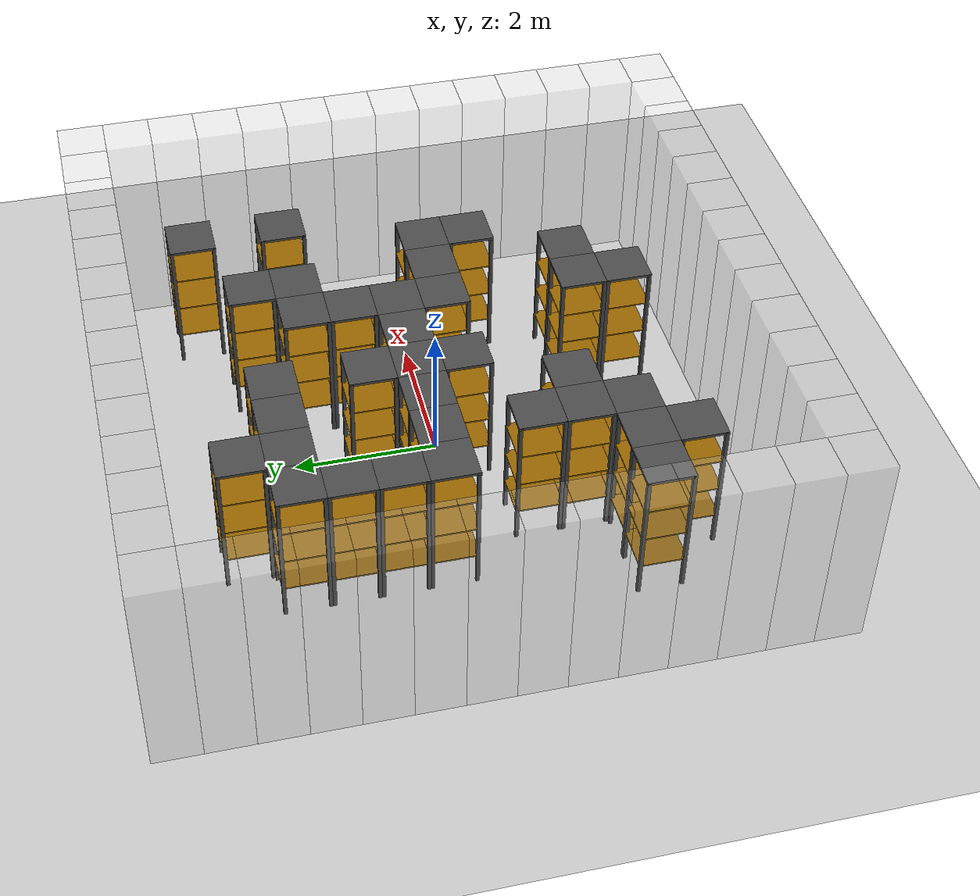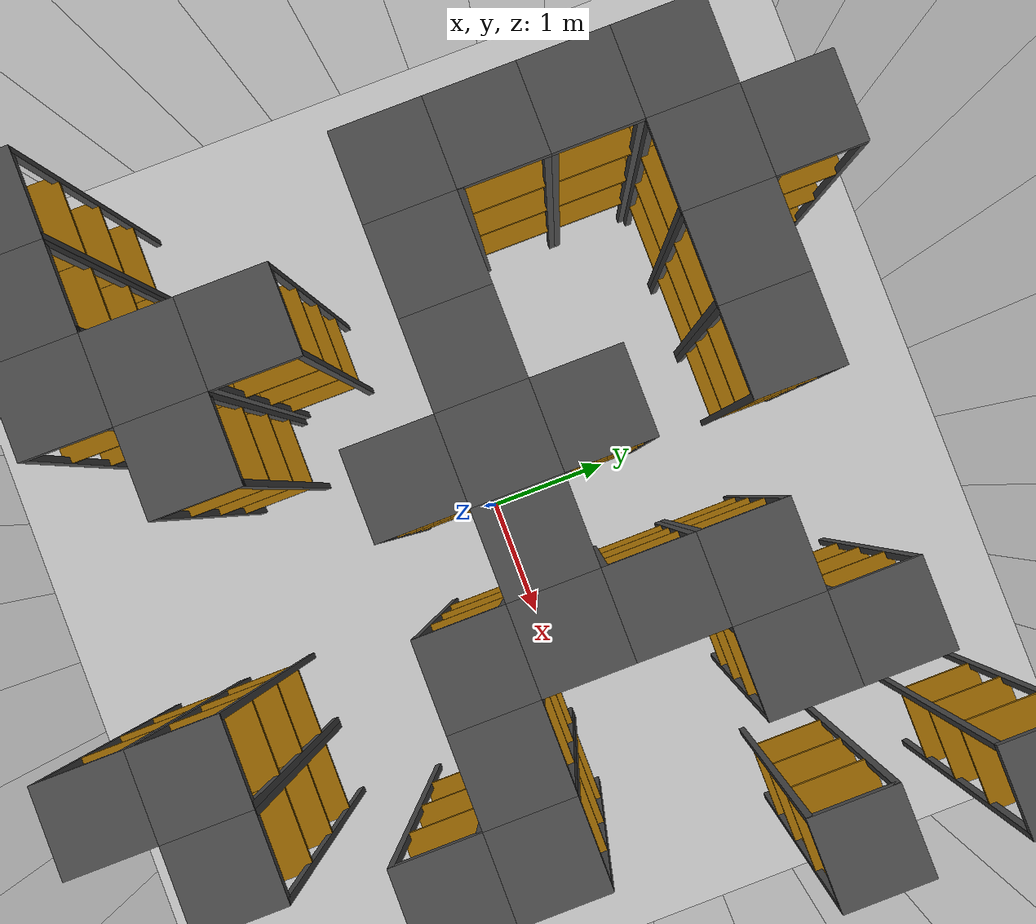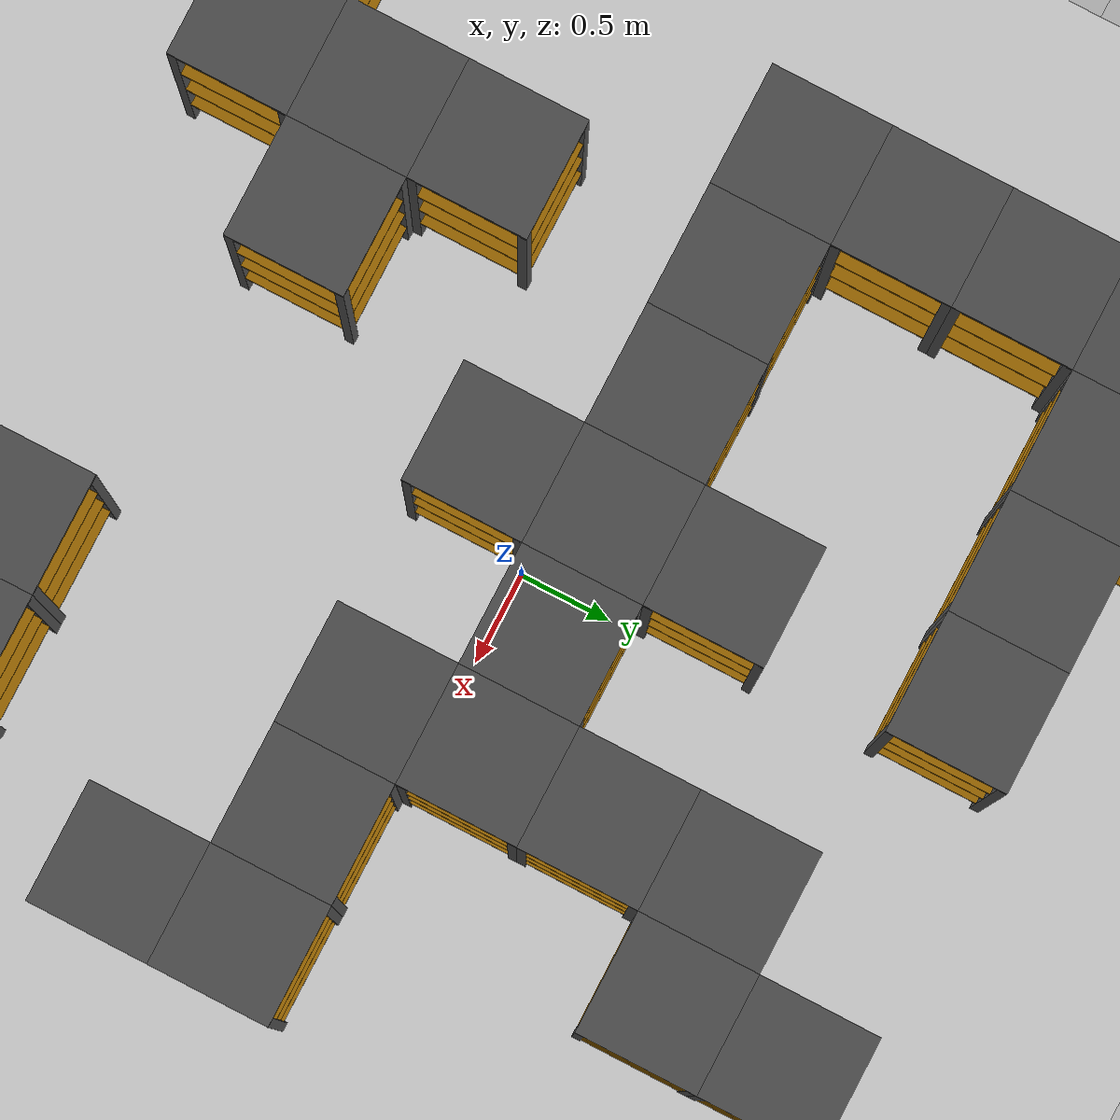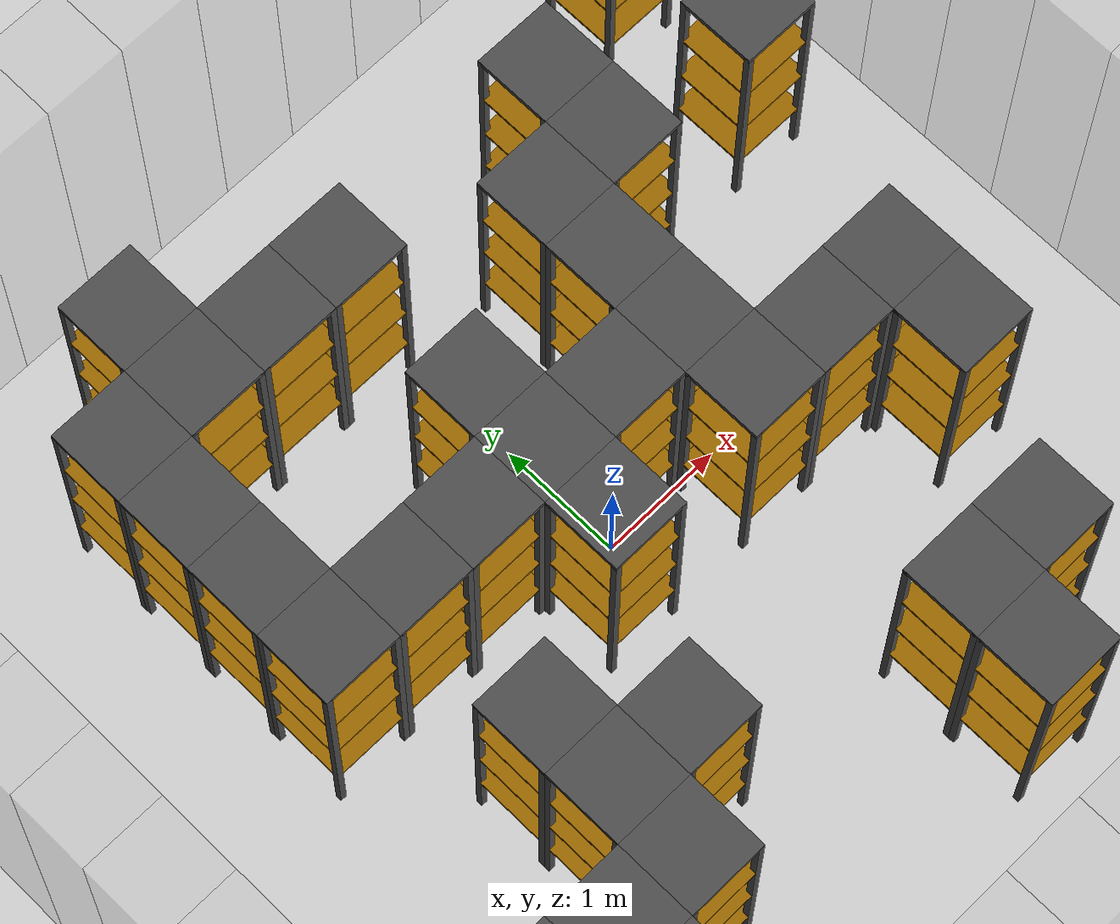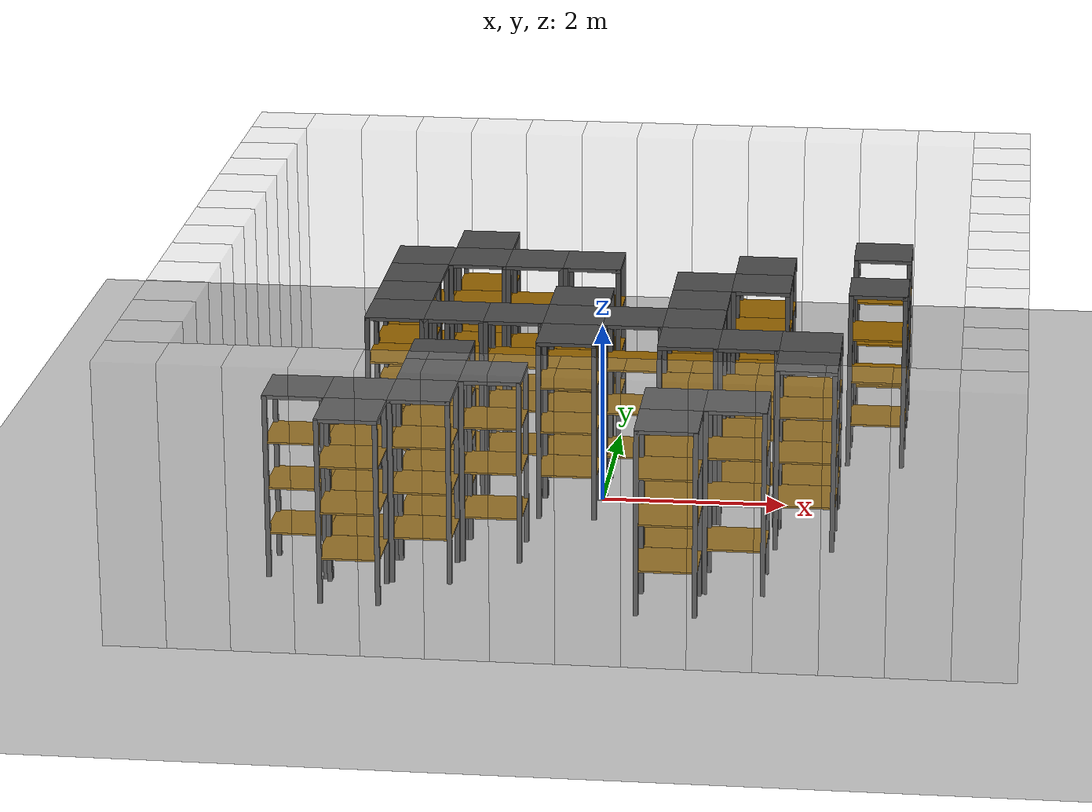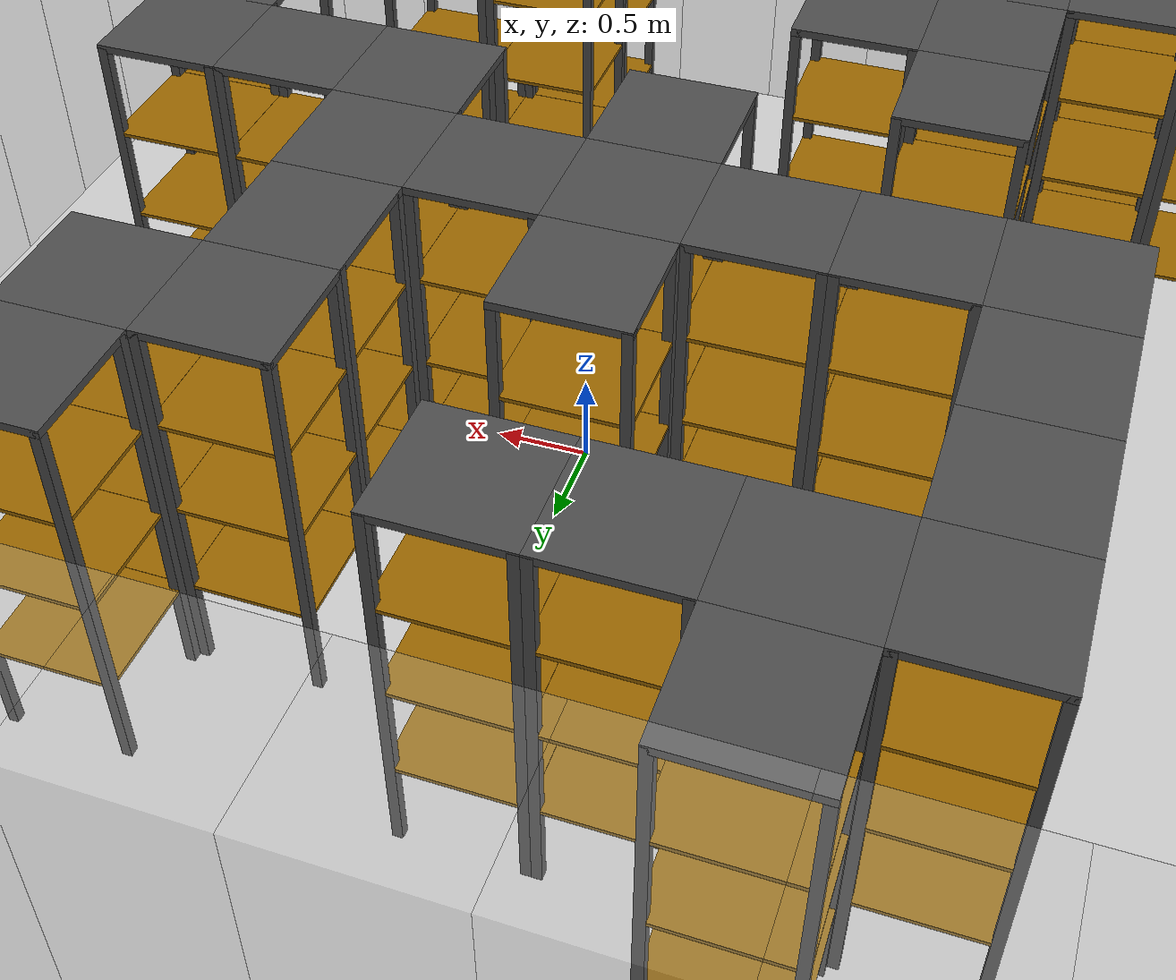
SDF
<sdf version="1.6">
 <world name="default">
  <light name="sun" type="directional">
   <pose>0 0 10 0 -0 0</pose>
   <diffuse>0.8 0.8 0.8 1</diffuse>
   <specular>0.2 0.2 0.2 1</specular>
   <attenuation>
    <range>1000</range>
    <constant>0.9</constant>
    <linear>0.01</linear>
    <quadratic>0.001</quadratic>
   </attenuation>
   <direction>-0.5 0.1 -0.9</direction>
  </light>
  <model name="ground_plane">
   <static>1</static>
   <link name="link">
    <collision name="collision">
     <geometry><plane><normal>0 0 1</normal><size>100 100</size></plane></geometry>
     <surface><friction><ode><mu>100</mu><mu2>50</mu2></ode></friction></surface>
    </collision>
    <visual name="visual">
     <cast_shadows>0</cast_shadows>
     <geometry><plane><normal>0 0 1</normal><size>100 100</size></plane></geometry>
     <material>
      <script><uri>file://media/materials/scripts/gazebo.material</uri><name>Gazebo/Grey</name></script>
     </material>
    </visual>
   </link>
  </model>
  <gravity>0 0 -9.8</gravity>
  <magnetic_field>6e-06 2.3e-05 -4.2e-05</magnetic_field>
  <atmosphere type="adiabatic"/>
  <physics name="default_physics" default="0" type="ode">
   <max_step_size>0.001</max_step_size>
   <real_time_factor>1</real_time_factor>
   <real_time_update_rate>1000</real_time_update_rate>
  </physics>
  <scene><ambient>0.4 0.4 0.4 1</ambient><background>0.7 0.7 0.7 1</background><shadows>1</shadows></scene>
  <spherical_coordinates>
   <surface_model>EARTH_WGS84</surface_model>
   <latitude_deg>0</latitude_deg>
   <longitude_deg>0</longitude_deg>
   <elevation>0</elevation>
   <heading_deg>0</heading_deg>
  </spherical_coordinates>
  <model name="pole_0_0">
   <static>1</static>
   <link name="main_block">
    <pose>0 0 1.5 0 -0 0</pose>
    <collision name="collision"><geometry><box><size>0.65 0.65 3</size></box></geometry></collision>
    <visual name="visual">
     <geometry><box><size>0.65 0.65 3</size></box></geometry>
     <material><ambient>0.5 0.5 0.5 0.25</ambient><diffuse>0.75 0.75 0.75 0.25</diffuse></material>
    </visual>
   </link>
   <pose>-4.225 -4.225 0 0 -0 0</pose>
  </model>
  <model name="pole_0_1">
   <static>1</static>
   <link name="main_block">
    <pose>0 0 1.5 0 -0 0</pose>
    <collision name="collision"><geometry><box><size>0.65 0.65 3</size></box></geometry></collision>
    <visual name="visual">
     <geometry><box><size>0.65 0.65 3</size></box></geometry>
     <material><ambient>0.5 0.5 0.5 0.25</ambient><diffuse>0.75 0.75 0.75 0.25</diffuse></material>
    </visual>
   </link>
   <pose>-3.575 -4.225 0 0 -0 0</pose>
  </model>
  <model name="pole_0_2">
   <static>1</static>
   <link name="main_block">
    <pose>0 0 1.5 0 -0 0</pose>
    <collision name="collision"><geometry><box><size>0.65 0.65 3</size></box></geometry></collision>
    <visual name="visual">
     <geometry><box><size>0.65 0.65 3</size></box></geometry>
     <material><ambient>0.5 0.5 0.5 0.25</ambient><diffuse>0.75 0.75 0.75 0.25</diffuse></material>
    </visual>
   </link>
   <pose>-2.925 -4.225 0 0 -0 0</pose>
  </model>
  <model name="pole_0_3">
   <static>1</static>
   <link name="main_block">
    <pose>0 0 1.5 0 -0 0</pose>
    <collision name="collision"><geometry><box><size>0.65 0.65 3</size></box></geometry></collision>
    <visual name="visual">
     <geometry><box><size>0.65 0.65 3</size></box></geometry>
     <material><ambient>0.5 0.5 0.5 0.25</ambient><diffuse>0.75 0.75 0.75 0.25</diffuse></material>
    </visual>
   </link>
   <pose>-2.275 -4.225 0 0 -0 0</pose>
  </model>
  <model name="pole_0_4">
   <static>1</static>
   <link name="main_block">
    <pose>0 0 1.5 0 -0 0</pose>
    <collision name="collision"><geometry><box><size>0.65 0.65 3</size></box></geometry></collision>
    <visual name="visual">
     <geometry><box><size>0.65 0.65 3</size></box></geometry>
     <material><ambient>0.5 0.5 0.5 0.25</ambient><diffuse>0.75 0.75 0.75 0.25</diffuse></material>
    </visual>
   </link>
   <pose>-1.625 -4.225 0 0 -0 0</pose>
  </model>
  <model name="pole_0_5">
   <static>1</static>
   <link name="main_block">
    <pose>0 0 1.5 0 -0 0</pose>
    <collision name="collision"><geometry><box><size>0.65 0.65 3</size></box></geometry></collision>
    <visual name="visual">
     <geometry><box><size>0.65 0.65 3</size></box></geometry>
     <material><ambient>0.5 0.5 0.5 0.25</ambient><diffuse>0.75 0.75 0.75 0.25</diffuse></material>
    </visual>
   </link>
   <pose>-0.975 -4.225 0 0 -0 0</pose>
  </model>
  <model name="pole_0_6">
   <static>1</static>
   <link name="main_block">
    <pose>0 0 1.5 0 -0 0</pose>
    <collision name="collision"><geometry><box><size>0.65 0.65 3</size></box></geometry></collision>
    <visual name="visual">
     <geometry><box><size>0.65 0.65 3</size></box></geometry>
     <material><ambient>0.5 0.5 0.5 0.25</ambient><diffuse>0.75 0.75 0.75 0.25</diffuse></material>
    </visual>
   </link>
   <pose>-0.325 -4.225 0 0 -0 0</pose>
  </model>
  <model name="pole_0_7">
   <static>1</static>
   <link name="main_block">
    <pose>0 0 1.5 0 -0 0</pose>
    <collision name="collision"><geometry><box><size>0.65 0.65 3</size></box></geometry></collision>
    <visual name="visual">
     <geometry><box><size>0.65 0.65 3</size></box></geometry>
     <material><ambient>0.5 0.5 0.5 0.25</ambient><diffuse>0.75 0.75 0.75 0.25</diffuse></material>
    </visual>
   </link>
   <pose>0.325 -4.225 0 0 -0 0</pose>
  </model>
  <model name="pole_0_8">
   <static>1</static>
   <link name="main_block">
    <pose>0 0 1.5 0 -0 0</pose>
    <collision name="collision"><geometry><box><size>0.65 0.65 3</size></box></geometry></collision>
    <visual name="visual">
     <geometry><box><size>0.65 0.65 3</size></box></geometry>
     <material><ambient>0.5 0.5 0.5 0.25</ambient><diffuse>0.75 0.75 0.75 0.25</diffuse></material>
    </visual>
   </link>
   <pose>0.975 -4.225 0 0 -0 0</pose>
  </model>
  <model name="pole_0_9">
   <static>1</static>
   <link name="main_block">
    <pose>0 0 1.5 0 -0 0</pose>
    <collision name="collision"><geometry><box><size>0.65 0.65 3</size></box></geometry></collision>
    <visual name="visual">
     <geometry><box><size>0.65 0.65 3</size></box></geometry>
     <material><ambient>0.5 0.5 0.5 0.25</ambient><diffuse>0.75 0.75 0.75 0.25</diffuse></material>
    </visual>
   </link>
   <pose>1.625 -4.225 0 0 -0 0</pose>
  </model>
  <model name="pole_0_10">
   <static>1</static>
   <link name="main_block">
    <pose>0 0 1.5 0 -0 0</pose>
    <collision name="collision"><geometry><box><size>0.65 0.65 3</size></box></geometry></collision>
    <visual name="visual">
     <geometry><box><size>0.65 0.65 3</size></box></geometry>
     <material><ambient>0.5 0.5 0.5 0.25</ambient><diffuse>0.75 0.75 0.75 0.25</diffuse></material>
    </visual>
   </link>
   <pose>2.275 -4.225 0 0 -0 0</pose>
  </model>
  <model name="pole_0_11">
   <static>1</static>
   <link name="main_block">
    <pose>0 0 1.5 0 -0 0</pose>
    <collision name="collision"><geometry><box><size>0.65 0.65 3</size></box></geometry></collision>
    <visual name="visual">
     <geometry><box><size>0.65 0.65 3</size></box></geometry>
     <material><ambient>0.5 0.5 0.5 0.25</ambient><diffuse>0.75 0.75 0.75 0.25</diffuse></material>
    </visual>
   </link>
   <pose>2.925 -4.225 0 0 -0 0</pose>
  </model>
  <model name="pole_0_12">
   <static>1</static>
   <link name="main_block">
    <pose>0 0 1.5 0 -0 0</pose>
    <collision name="collision"><geometry><box><size>0.65 0.65 3</size></box></geometry></collision>
    <visual name="visual">
     <geometry><box><size>0.65 0.65 3</size></box></geometry>
     <material><ambient>0.5 0.5 0.5 0.25</ambient><diffuse>0.75 0.75 0.75 0.25</diffuse></material>
    </visual>
   </link>
   <pose>3.575 -4.225 0 0 -0 0</pose>
  </model>
  <model name="pole_0_13">
   <static>1</static>
   <link name="main_block">
    <pose>0 0 1.5 0 -0 0</pose>
    <collision name="collision"><geometry><box><size>0.65 0.65 3</size></box></geometry></collision>
    <visual name="visual">
     <geometry><box><size>0.65 0.65 3</size></box></geometry>
     <material><ambient>0.5 0.5 0.5 0.25</ambient><diffuse>0.75 0.75 0.75 0.25</diffuse></material>
    </visual>
   </link>
   <pose>4.225 -4.225 0 0 -0 0</pose>
  </model>
  <model name="pole_1_0">
   <static>1</static>
   <link name="main_block">
    <pose>0 0 1.5 0 -0 0</pose>
    <collision name="collision"><geometry><box><size>0.65 0.65 3</size></box></geometry></collision>
    <visual name="visual">
     <geometry><box><size>0.65 0.65 3</size></box></geometry>
     <material><ambient>0.5 0.5 0.5 0.25</ambient><diffuse>0.75 0.75 0.75 0.25</diffuse></material>
    </visual>
   </link>
   <pose>-4.225 -3.575 0 0 -0 0</pose>
  </model>
  <model name="pole_1_13">
   <static>1</static>
   <link name="main_block">
    <pose>0 0 1.5 0 -0 0</pose>
    <collision name="collision"><geometry><box><size>0.65 0.65 3</size></box></geometry></collision>
    <visual name="visual">
     <geometry><box><size>0.65 0.65 3</size></box></geometry>
     <material><ambient>0.5 0.5 0.5 0.25</ambient><diffuse>0.75 0.75 0.75 0.25</diffuse></material>
    </visual>
   </link>
   <pose>4.225 -3.575 0 0 -0 0</pose>
  </model>
  <model name="pole_2_0">
   <static>1</static>
   <link name="main_block">
    <pose>0 0 1.5 0 -0 0</pose>
    <collision name="collision"><geometry><box><size>0.65 0.65 3</size></box></geometry></collision>
    <visual name="visual">
     <geometry><box><size>0.65 0.65 3</size></box></geometry>
     <material><ambient>0.5 0.5 0.5 0.25</ambient><diffuse>0.75 0.75 0.75 0.25</diffuse></material>
    </visual>
   </link>
   <pose>-4.225 -2.925 0 0 -0 0</pose>
  </model>
  <model name="warehouse_shelf_2_3">
   <static>1</static>
   <link name="main_block">
    <pose>0 0 1.25 0 -0 0</pose>
    <collision name="collision"><geometry><box><size>0.65 0.65 1.5</size></box></geometry></collision>
   </link>
   <link name="leg_1">
    <pose>0.3 0.3 1 0 -0 0</pose>
    <collision name="collision"><geometry><box><size>0.05 0.05 2</size></box></geometry></collision>
    <visual name="visual">
     <geometry><box><size>0.05 0.05 2</size></box></geometry>
     <material><ambient>0.2 0.2 0.2 1</ambient><diffuse>0.3 0.3 0.3 1</diffuse></material>
    </visual>
   </link>
   <link name="leg_2">
    <pose>-0.3 0.3 1 0 -0 0</pose>
    <collision name="collision"><geometry><box><size>0.05 0.05 2</size></box></geometry></collision>
    <visual name="visual">
     <geometry><box><size>0.05 0.05 2</size></box></geometry>
     <material><ambient>0.2 0.2 0.2 1</ambient><diffuse>0.3 0.3 0.3 1</diffuse></material>
    </visual>
   </link>
   <link name="leg_3">
    <pose>-0.3 -0.3 1 0 -0 0</pose>
    <collision name="collision"><geometry><box><size>0.05 0.05 2</size></box></geometry></collision>
    <visual name="visual">
     <geometry><box><size>0.05 0.05 2</size></box></geometry>
     <material><ambient>0.2 0.2 0.2 1</ambient><diffuse>0.3 0.3 0.3 1</diffuse></material>
    </visual>
   </link>
   <link name="leg_4">
    <pose>0.3 -0.3 1 0 -0 0</pose>
    <collision name="collision"><geometry><box><size>0.05 0.05 2</size></box></geometry></collision>
    <visual name="visual">
     <geometry><box><size>0.05 0.05 2</size></box></geometry>
     <material><ambient>0.2 0.2 0.2 1</ambient><diffuse>0.3 0.3 0.3 1</diffuse></material>
    </visual>
   </link>
   <link name="shelf_0">
    <pose>0 0 0.49 0 -0 0</pose>
    <visual name="visual">
     <geometry><box><size>0.649 0.649 0.02</size></box></geometry>
     <material><ambient>0.2 0.05 0 1</ambient><diffuse>0.6 0.4 0 1</diffuse></material>
    </visual>
   </link>
   <link name="shelf_1">
    <pose>0 0 0.99 0 -0 0</pose>
    <visual name="visual">
     <geometry><box><size>0.649 0.649 0.02</size></box></geometry>
     <material><ambient>0.2 0.05 0 1</ambient><diffuse>0.6 0.4 0 1</diffuse></material>
    </visual>
   </link>
   <link name="shelf_2">
    <pose>0 0 1.49 0 -0 0</pose>
    <visual name="visual">
     <geometry><box><size>0.649 0.649 0.02</size></box></geometry>
     <material><ambient>0.2 0.05 0 1</ambient><diffuse>0.6 0.4 0 1</diffuse></material>
    </visual>
   </link>
   <link name="shelf_top">
    <pose>0 0 1.99 0 -0 0</pose>
    <visual name="visual">
     <geometry><box><size>0.65 0.65 0.04</size></box></geometry>
     <material><ambient>0.2 0.2 0.2 1</ambient><diffuse>0.3 0.3 0.3 1</diffuse></material>
    </visual>
   </link>
   <pose>-2.275 -2.925 0 0 -0 0</pose>
  </model>
  <model name="warehouse_shelf_2_8">
   <static>1</static>
   <link name="main_block">
    <pose>0 0 1.25 0 -0 0</pose>
    <collision name="collision"><geometry><box><size>0.65 0.65 1.5</size></box></geometry></collision>
   </link>
   <link name="leg_1">
    <pose>0.3 0.3 1 0 -0 0</pose>
    <collision name="collision"><geometry><box><size>0.05 0.05 2</size></box></geometry></collision>
    <visual name="visual">
     <geometry><box><size>0.05 0.05 2</size></box></geometry>
     <material><ambient>0.2 0.2 0.2 1</ambient><diffuse>0.3 0.3 0.3 1</diffuse></material>
    </visual>
   </link>
   <link name="leg_2">
    <pose>-0.3 0.3 1 0 -0 0</pose>
    <collision name="collision"><geometry><box><size>0.05 0.05 2</size></box></geometry></collision>
    <visual name="visual">
     <geometry><box><size>0.05 0.05 2</size></box></geometry>
     <material><ambient>0.2 0.2 0.2 1</ambient><diffuse>0.3 0.3 0.3 1</diffuse></material>
    </visual>
   </link>
   <link name="leg_3">
    <pose>-0.3 -0.3 1 0 -0 0</pose>
    <collision name="collision"><geometry><box><size>0.05 0.05 2</size></box></geometry></collision>
    <visual name="visual">
     <geometry><box><size>0.05 0.05 2</size></box></geometry>
     <material><ambient>0.2 0.2 0.2 1</ambient><diffuse>0.3 0.3 0.3 1</diffuse></material>
    </visual>
   </link>
   <link name="leg_4">
    <pose>0.3 -0.3 1 0 -0 0</pose>
    <collision name="collision"><geometry><box><size>0.05 0.05 2</size></box></geometry></collision>
    <visual name="visual">
     <geometry><box><size>0.05 0.05 2</size></box></geometry>
     <material><ambient>0.2 0.2 0.2 1</ambient><diffuse>0.3 0.3 0.3 1</diffuse></material>
    </visual>
   </link>
   <link name="shelf_0">
    <pose>0 0 0.49 0 -0 0</pose>
    <visual name="visual">
     <geometry><box><size>0.649 0.649 0.02</size></box></geometry>
     <material><ambient>0.2 0.05 0 1</ambient><diffuse>0.6 0.4 0 1</diffuse></material>
    </visual>
   </link>
   <link name="shelf_1">
    <pose>0 0 0.99 0 -0 0</pose>
    <visual name="visual">
     <geometry><box><size>0.649 0.649 0.02</size></box></geometry>
     <material><ambient>0.2 0.05 0 1</ambient><diffuse>0.6 0.4 0 1</diffuse></material>
    </visual>
   </link>
   <link name="shelf_2">
    <pose>0 0 1.49 0 -0 0</pose>
    <visual name="visual">
     <geometry><box><size>0.649 0.649 0.02</size></box></geometry>
     <material><ambient>0.2 0.05 0 1</ambient><diffuse>0.6 0.4 0 1</diffuse></material>
    </visual>
   </link>
   <link name="shelf_top">
    <pose>0 0 1.99 0 -0 0</pose>
    <visual name="visual">
     <geometry><box><size>0.65 0.65 0.04</size></box></geometry>
     <material><ambient>0.2 0.2 0.2 1</ambient><diffuse>0.3 0.3 0.3 1</diffuse></material>
    </visual>
   </link>
   <pose>0.975 -2.925 0 0 -0 0</pose>
  </model>
  <model name="pole_2_13">
   <static>1</static>
   <link name="main_block">
    <pose>0 0 1.5 0 -0 0</pose>
    <collision name="collision"><geometry><box><size>0.65 0.65 3</size></box></geometry></collision>
    <visual name="visual">
     <geometry><box><size>0.65 0.65 3</size></box></geometry>
     <material><ambient>0.5 0.5 0.5 0.25</ambient><diffuse>0.75 0.75 0.75 0.25</diffuse></material>
    </visual>
   </link>
   <pose>4.225 -2.925 0 0 -0 0</pose>
  </model>
  <model name="pole_3_0">
   <static>1</static>
   <link name="main_block">
    <pose>0 0 1.5 0 -0 0</pose>
    <collision name="collision"><geometry><box><size>0.65 0.65 3</size></box></geometry></collision>
    <visual name="visual">
     <geometry><box><size>0.65 0.65 3</size></box></geometry>
     <material><ambient>0.5 0.5 0.5 0.25</ambient><diffuse>0.75 0.75 0.75 0.25</diffuse></material>
    </visual>
   </link>
   <pose>-4.225 -2.275 0 0 -0 0</pose>
  </model>
  <model name="warehouse_shelf_3_2">
   <static>1</static>
   <link name="main_block">
    <pose>0 0 1.25 0 -0 0</pose>
    <collision name="collision"><geometry><box><size>0.65 0.65 1.5</size></box></geometry></collision>
   </link>
   <link name="leg_1">
    <pose>0.3 0.3 1 0 -0 0</pose>
    <collision name="collision"><geometry><box><size>0.05 0.05 2</size></box></geometry></collision>
    <visual name="visual">
     <geometry><box><size>0.05 0.05 2</size></box></geometry>
     <material><ambient>0.2 0.2 0.2 1</ambient><diffuse>0.3 0.3 0.3 1</diffuse></material>
    </visual>
   </link>
   <link name="leg_2">
    <pose>-0.3 0.3 1 0 -0 0</pose>
    <collision name="collision"><geometry><box><size>0.05 0.05 2</size></box></geometry></collision>
    <visual name="visual">
     <geometry><box><size>0.05 0.05 2</size></box></geometry>
     <material><ambient>0.2 0.2 0.2 1</ambient><diffuse>0.3 0.3 0.3 1</diffuse></material>
    </visual>
   </link>
   <link name="leg_3">
    <pose>-0.3 -0.3 1 0 -0 0</pose>
    <collision name="collision"><geometry><box><size>0.05 0.05 2</size></box></geometry></collision>
    <visual name="visual">
     <geometry><box><size>0.05 0.05 2</size></box></geometry>
     <material><ambient>0.2 0.2 0.2 1</ambient><diffuse>0.3 0.3 0.3 1</diffuse></material>
    </visual>
   </link>
   <link name="leg_4">
    <pose>0.3 -0.3 1 0 -0 0</pose>
    <collision name="collision"><geometry><box><size>0.05 0.05 2</size></box></geometry></collision>
    <visual name="visual">
     <geometry><box><size>0.05 0.05 2</size></box></geometry>
     <material><ambient>0.2 0.2 0.2 1</ambient><diffuse>0.3 0.3 0.3 1</diffuse></material>
    </visual>
   </link>
   <link name="shelf_0">
    <pose>0 0 0.49 0 -0 0</pose>
    <visual name="visual">
     <geometry><box><size>0.649 0.649 0.02</size></box></geometry>
     <material><ambient>0.2 0.05 0 1</ambient><diffuse>0.6 0.4 0 1</diffuse></material>
    </visual>
   </link>
   <link name="shelf_1">
    <pose>0 0 0.99 0 -0 0</pose>
    <visual name="visual">
     <geometry><box><size>0.649 0.649 0.02</size></box></geometry>
     <material><ambient>0.2 0.05 0 1</ambient><diffuse>0.6 0.4 0 1</diffuse></material>
    </visual>
   </link>
   <link name="shelf_2">
    <pose>0 0 1.49 0 -0 0</pose>
    <visual name="visual">
     <geometry><box><size>0.649 0.649 0.02</size></box></geometry>
     <material><ambient>0.2 0.05 0 1</ambient><diffuse>0.6 0.4 0 1</diffuse></material>
    </visual>
   </link>
   <link name="shelf_top">
    <pose>0 0 1.99 0 -0 0</pose>
    <visual name="visual">
     <geometry><box><size>0.65 0.65 0.04</size></box></geometry>
     <material><ambient>0.2 0.2 0.2 1</ambient><diffuse>0.3 0.3 0.3 1</diffuse></material>
    </visual>
   </link>
   <pose>-2.925 -2.275 0 0 -0 0</pose>
  </model>
  <model name="warehouse_shelf_3_3">
   <static>1</static>
   <link name="main_block">
    <pose>0 0 1.25 0 -0 0</pose>
    <collision name="collision"><geometry><box><size>0.65 0.65 1.5</size></box></geometry></collision>
   </link>
   <link name="leg_1">
    <pose>0.3 0.3 1 0 -0 0</pose>
    <collision name="collision"><geometry><box><size>0.05 0.05 2</size></box></geometry></collision>
    <visual name="visual">
     <geometry><box><size>0.05 0.05 2</size></box></geometry>
     <material><ambient>0.2 0.2 0.2 1</ambient><diffuse>0.3 0.3 0.3 1</diffuse></material>
    </visual>
   </link>
   <link name="leg_2">
    <pose>-0.3 0.3 1 0 -0 0</pose>
    <collision name="collision"><geometry><box><size>0.05 0.05 2</size></box></geometry></collision>
    <visual name="visual">
     <geometry><box><size>0.05 0.05 2</size></box></geometry>
     <material><ambient>0.2 0.2 0.2 1</ambient><diffuse>0.3 0.3 0.3 1</diffuse></material>
    </visual>
   </link>
   <link name="leg_3">
    <pose>-0.3 -0.3 1 0 -0 0</pose>
    <collision name="collision"><geometry><box><size>0.05 0.05 2</size></box></geometry></collision>
    <visual name="visual">
     <geometry><box><size>0.05 0.05 2</size></box></geometry>
     <material><ambient>0.2 0.2 0.2 1</ambient><diffuse>0.3 0.3 0.3 1</diffuse></material>
    </visual>
   </link>
   <link name="leg_4">
    <pose>0.3 -0.3 1 0 -0 0</pose>
    <collision name="collision"><geometry><box><size>0.05 0.05 2</size></box></geometry></collision>
    <visual name="visual">
     <geometry><box><size>0.05 0.05 2</size></box></geometry>
     <material><ambient>0.2 0.2 0.2 1</ambient><diffuse>0.3 0.3 0.3 1</diffuse></material>
    </visual>
   </link>
   <link name="shelf_0">
    <pose>0 0 0.49 0 -0 0</pose>
    <visual name="visual">
     <geometry><box><size>0.649 0.649 0.02</size></box></geometry>
     <material><ambient>0.2 0.05 0 1</ambient><diffuse>0.6 0.4 0 1</diffuse></material>
    </visual>
   </link>
   <link name="shelf_1">
    <pose>0 0 0.99 0 -0 0</pose>
    <visual name="visual">
     <geometry><box><size>0.649 0.649 0.02</size></box></geometry>
     <material><ambient>0.2 0.05 0 1</ambient><diffuse>0.6 0.4 0 1</diffuse></material>
    </visual>
   </link>
   <link name="shelf_2">
    <pose>0 0 1.49 0 -0 0</pose>
    <visual name="visual">
     <geometry><box><size>0.649 0.649 0.02</size></box></geometry>
     <material><ambient>0.2 0.05 0 1</ambient><diffuse>0.6 0.4 0 1</diffuse></material>
    </visual>
   </link>
   <link name="shelf_top">
    <pose>0 0 1.99 0 -0 0</pose>
    <visual name="visual">
     <geometry><box><size>0.65 0.65 0.04</size></box></geometry>
     <material><ambient>0.2 0.2 0.2 1</ambient><diffuse>0.3 0.3 0.3 1</diffuse></material>
    </visual>
   </link>
   <pose>-2.275 -2.275 0 0 -0 0</pose>
  </model>
  <model name="warehouse_shelf_3_4">
   <static>1</static>
   <link name="main_block">
    <pose>0 0 1.25 0 -0 0</pose>
    <collision name="collision"><geometry><box><size>0.65 0.65 1.5</size></box></geometry></collision>
   </link>
   <link name="leg_1">
    <pose>0.3 0.3 1 0 -0 0</pose>
    <collision name="collision"><geometry><box><size>0.05 0.05 2</size></box></geometry></collision>
    <visual name="visual">
     <geometry><box><size>0.05 0.05 2</size></box></geometry>
     <material><ambient>0.2 0.2 0.2 1</ambient><diffuse>0.3 0.3 0.3 1</diffuse></material>
    </visual>
   </link>
   <link name="leg_2">
    <pose>-0.3 0.3 1 0 -0 0</pose>
    <collision name="collision"><geometry><box><size>0.05 0.05 2</size></box></geometry></collision>
    <visual name="visual">
     <geometry><box><size>0.05 0.05 2</size></box></geometry>
     <material><ambient>0.2 0.2 0.2 1</ambient><diffuse>0.3 0.3 0.3 1</diffuse></material>
    </visual>
   </link>
   <link name="leg_3">
    <pose>-0.3 -0.3 1 0 -0 0</pose>
    <collision name="collision"><geometry><box><size>0.05 0.05 2</size></box></geometry></collision>
    <visual name="visual">
     <geometry><box><size>0.05 0.05 2</size></box></geometry>
     <material><ambient>0.2 0.2 0.2 1</ambient><diffuse>0.3 0.3 0.3 1</diffuse></material>
    </visual>
   </link>
   <link name="leg_4">
    <pose>0.3 -0.3 1 0 -0 0</pose>
    <collision name="collision"><geometry><box><size>0.05 0.05 2</size></box></geometry></collision>
    <visual name="visual">
     <geometry><box><size>0.05 0.05 2</size></box></geometry>
     <material><ambient>0.2 0.2 0.2 1</ambient><diffuse>0.3 0.3 0.3 1</diffuse></material>
    </visual>
   </link>
   <link name="shelf_0">
    <pose>0 0 0.49 0 -0 0</pose>
    <visual name="visual">
     <geometry><box><size>0.649 0.649 0.02</size></box></geometry>
     <material><ambient>0.2 0.05 0 1</ambient><diffuse>0.6 0.4 0 1</diffuse></material>
    </visual>
   </link>
   <link name="shelf_1">
    <pose>0 0 0.99 0 -0 0</pose>
    <visual name="visual">
     <geometry><box><size>0.649 0.649 0.02</size></box></geometry>
     <material><ambient>0.2 0.05 0 1</ambient><diffuse>0.6 0.4 0 1</diffuse></material>
    </visual>
   </link>
   <link name="shelf_2">
    <pose>0 0 1.49 0 -0 0</pose>
    <visual name="visual">
     <geometry><box><size>0.649 0.649 0.02</size></box></geometry>
     <material><ambient>0.2 0.05 0 1</ambient><diffuse>0.6 0.4 0 1</diffuse></material>
    </visual>
   </link>
   <link name="shelf_top">
    <pose>0 0 1.99 0 -0 0</pose>
    <visual name="visual">
     <geometry><box><size>0.65 0.65 0.04</size></box></geometry>
     <material><ambient>0.2 0.2 0.2 1</ambient><diffuse>0.3 0.3 0.3 1</diffuse></material>
    </visual>
   </link>
   <pose>-1.625 -2.275 0 0 -0 0</pose>
  </model>
  <model name="warehouse_shelf_3_8">
   <static>1</static>
   <link name="main_block">
    <pose>0 0 1.25 0 -0 0</pose>
    <collision name="collision"><geometry><box><size>0.65 0.65 1.5</size></box></geometry></collision>
   </link>
   <link name="leg_1">
    <pose>0.3 0.3 1 0 -0 0</pose>
    <collision name="collision"><geometry><box><size>0.05 0.05 2</size></box></geometry></collision>
    <visual name="visual">
     <geometry><box><size>0.05 0.05 2</size></box></geometry>
     <material><ambient>0.2 0.2 0.2 1</ambient><diffuse>0.3 0.3 0.3 1</diffuse></material>
    </visual>
   </link>
   <link name="leg_2">
    <pose>-0.3 0.3 1 0 -0 0</pose>
    <collision name="collision"><geometry><box><size>0.05 0.05 2</size></box></geometry></collision>
    <visual name="visual">
     <geometry><box><size>0.05 0.05 2</size></box></geometry>
     <material><ambient>0.2 0.2 0.2 1</ambient><diffuse>0.3 0.3 0.3 1</diffuse></material>
    </visual>
   </link>
   <link name="leg_3">
    <pose>-0.3 -0.3 1 0 -0 0</pose>
    <collision name="collision"><geometry><box><size>0.05 0.05 2</size></box></geometry></collision>
    <visual name="visual">
     <geometry><box><size>0.05 0.05 2</size></box></geometry>
     <material><ambient>0.2 0.2 0.2 1</ambient><diffuse>0.3 0.3 0.3 1</diffuse></material>
    </visual>
   </link>
   <link name="leg_4">
    <pose>0.3 -0.3 1 0 -0 0</pose>
    <collision name="collision"><geometry><box><size>0.05 0.05 2</size></box></geometry></collision>
    <visual name="visual">
     <geometry><box><size>0.05 0.05 2</size></box></geometry>
     <material><ambient>0.2 0.2 0.2 1</ambient><diffuse>0.3 0.3 0.3 1</diffuse></material>
    </visual>
   </link>
   <link name="shelf_0">
    <pose>0 0 0.49 0 -0 0</pose>
    <visual name="visual">
     <geometry><box><size>0.649 0.649 0.02</size></box></geometry>
     <material><ambient>0.2 0.05 0 1</ambient><diffuse>0.6 0.4 0 1</diffuse></material>
    </visual>
   </link>
   <link name="shelf_1">
    <pose>0 0 0.99 0 -0 0</pose>
    <visual name="visual">
     <geometry><box><size>0.649 0.649 0.02</size></box></geometry>
     <material><ambient>0.2 0.05 0 1</ambient><diffuse>0.6 0.4 0 1</diffuse></material>
    </visual>
   </link>
   <link name="shelf_2">
    <pose>0 0 1.49 0 -0 0</pose>
    <visual name="visual">
     <geometry><box><size>0.649 0.649 0.02</size></box></geometry>
     <material><ambient>0.2 0.05 0 1</ambient><diffuse>0.6 0.4 0 1</diffuse></material>
    </visual>
   </link>
   <link name="shelf_top">
    <pose>0 0 1.99 0 -0 0</pose>
    <visual name="visual">
     <geometry><box><size>0.65 0.65 0.04</size></box></geometry>
     <material><ambient>0.2 0.2 0.2 1</ambient><diffuse>0.3 0.3 0.3 1</diffuse></material>
    </visual>
   </link>
   <pose>0.975 -2.275 0 0 -0 0</pose>
  </model>
  <model name="warehouse_shelf_3_9">
   <static>1</static>
   <link name="main_block">
    <pose>0 0 1.25 0 -0 0</pose>
    <collision name="collision"><geometry><box><size>0.65 0.65 1.5</size></box></geometry></collision>
   </link>
   <link name="leg_1">
    <pose>0.3 0.3 1 0 -0 0</pose>
    <collision name="collision"><geometry><box><size>0.05 0.05 2</size></box></geometry></collision>
    <visual name="visual">
     <geometry><box><size>0.05 0.05 2</size></box></geometry>
     <material><ambient>0.2 0.2 0.2 1</ambient><diffuse>0.3 0.3 0.3 1</diffuse></material>
    </visual>
   </link>
   <link name="leg_2">
    <pose>-0.3 0.3 1 0 -0 0</pose>
    <collision name="collision"><geometry><box><size>0.05 0.05 2</size></box></geometry></collision>
    <visual name="visual">
     <geometry><box><size>0.05 0.05 2</size></box></geometry>
     <material><ambient>0.2 0.2 0.2 1</ambient><diffuse>0.3 0.3 0.3 1</diffuse></material>
    </visual>
   </link>
   <link name="leg_3">
    <pose>-0.3 -0.3 1 0 -0 0</pose>
    <collision name="collision"><geometry><box><size>0.05 0.05 2</size></box></geometry></collision>
    <visual name="visual">
     <geometry><box><size>0.05 0.05 2</size></box></geometry>
     <material><ambient>0.2 0.2 0.2 1</ambient><diffuse>0.3 0.3 0.3 1</diffuse></material>
    </visual>
   </link>
   <link name="leg_4">
    <pose>0.3 -0.3 1 0 -0 0</pose>
    <collision name="collision"><geometry><box><size>0.05 0.05 2</size></box></geometry></collision>
    <visual name="visual">
     <geometry><box><size>0.05 0.05 2</size></box></geometry>
     <material><ambient>0.2 0.2 0.2 1</ambient><diffuse>0.3 0.3 0.3 1</diffuse></material>
    </visual>
   </link>
   <link name="shelf_0">
    <pose>0 0 0.49 0 -0 0</pose>
    <visual name="visual">
     <geometry><box><size>0.649 0.649 0.02</size></box></geometry>
     <material><ambient>0.2 0.05 0 1</ambient><diffuse>0.6 0.4 0 1</diffuse></material>
    </visual>
   </link>
   <link name="shelf_1">
    <pose>0 0 0.99 0 -0 0</pose>
    <visual name="visual">
     <geometry><box><size>0.649 0.649 0.02</size></box></geometry>
     <material><ambient>0.2 0.05 0 1</ambient><diffuse>0.6 0.4 0 1</diffuse></material>
    </visual>
   </link>
   <link name="shelf_2">
    <pose>0 0 1.49 0 -0 0</pose>
    <visual name="visual">
     <geometry><box><size>0.649 0.649 0.02</size></box></geometry>
     <material><ambient>0.2 0.05 0 1</ambient><diffuse>0.6 0.4 0 1</diffuse></material>
    </visual>
   </link>
   <link name="shelf_top">
    <pose>0 0 1.99 0 -0 0</pose>
    <visual name="visual">
     <geometry><box><size>0.65 0.65 0.04</size></box></geometry>
     <material><ambient>0.2 0.2 0.2 1</ambient><diffuse>0.3 0.3 0.3 1</diffuse></material>
    </visual>
   </link>
   <pose>1.625 -2.275 0 0 -0 0</pose>
  </model>
  <model name="pole_3_13">
   <static>1</static>
   <link name="main_block">
    <pose>0 0 1.5 0 -0 0</pose>
    <collision name="collision"><geometry><box><size>0.65 0.65 3</size></box></geometry></collision>
    <visual name="visual">
     <geometry><box><size>0.65 0.65 3</size></box></geometry>
     <material><ambient>0.5 0.5 0.5 0.25</ambient><diffuse>0.75 0.75 0.75 0.25</diffuse></material>
    </visual>
   </link>
   <pose>4.225 -2.275 0 0 -0 0</pose>
  </model>
  <model name="pole_4_0">
   <static>1</static>
   <link name="main_block">
    <pose>0 0 1.5 0 -0 0</pose>
    <collision name="collision"><geometry><box><size>0.65 0.65 3</size></box></geometry></collision>
    <visual name="visual">
     <geometry><box><size>0.65 0.65 3</size></box></geometry>
     <material><ambient>0.5 0.5 0.5 0.25</ambient><diffuse>0.75 0.75 0.75 0.25</diffuse></material>
    </visual>
   </link>
   <pose>-4.225 -1.625 0 0 -0 0</pose>
  </model>
  <model name="warehouse_shelf_4_4">
   <static>1</static>
   <link name="main_block">
    <pose>0 0 1.25 0 -0 0</pose>
    <collision name="collision"><geometry><box><size>0.65 0.65 1.5</size></box></geometry></collision>
   </link>
   <link name="leg_1">
    <pose>0.3 0.3 1 0 -0 0</pose>
    <collision name="collision"><geometry><box><size>0.05 0.05 2</size></box></geometry></collision>
    <visual name="visual">
     <geometry><box><size>0.05 0.05 2</size></box></geometry>
     <material><ambient>0.2 0.2 0.2 1</ambient><diffuse>0.3 0.3 0.3 1</diffuse></material>
    </visual>
   </link>
   <link name="leg_2">
    <pose>-0.3 0.3 1 0 -0 0</pose>
    <collision name="collision"><geometry><box><size>0.05 0.05 2</size></box></geometry></collision>
    <visual name="visual">
     <geometry><box><size>0.05 0.05 2</size></box></geometry>
     <material><ambient>0.2 0.2 0.2 1</ambient><diffuse>0.3 0.3 0.3 1</diffuse></material>
    </visual>
   </link>
   <link name="leg_3">
    <pose>-0.3 -0.3 1 0 -0 0</pose>
    <collision name="collision"><geometry><box><size>0.05 0.05 2</size></box></geometry></collision>
    <visual name="visual">
     <geometry><box><size>0.05 0.05 2</size></box></geometry>
     <material><ambient>0.2 0.2 0.2 1</ambient><diffuse>0.3 0.3 0.3 1</diffuse></material>
    </visual>
   </link>
   <link name="leg_4">
    <pose>0.3 -0.3 1 0 -0 0</pose>
    <collision name="collision"><geometry><box><size>0.05 0.05 2</size></box></geometry></collision>
    <visual name="visual">
     <geometry><box><size>0.05 0.05 2</size></box></geometry>
     <material><ambient>0.2 0.2 0.2 1</ambient><diffuse>0.3 0.3 0.3 1</diffuse></material>
    </visual>
   </link>
   <link name="shelf_0">
    <pose>0 0 0.49 0 -0 0</pose>
    <visual name="visual">
     <geometry><box><size>0.649 0.649 0.02</size></box></geometry>
     <material><ambient>0.2 0.05 0 1</ambient><diffuse>0.6 0.4 0 1</diffuse></material>
    </visual>
   </link>
   <link name="shelf_1">
    <pose>0 0 0.99 0 -0 0</pose>
    <visual name="visual">
     <geometry><box><size>0.649 0.649 0.02</size></box></geometry>
     <material><ambient>0.2 0.05 0 1</ambient><diffuse>0.6 0.4 0 1</diffuse></material>
    </visual>
   </link>
   <link name="shelf_2">
    <pose>0 0 1.49 0 -0 0</pose>
    <visual name="visual">
     <geometry><box><size>0.649 0.649 0.02</size></box></geometry>
     <material><ambient>0.2 0.05 0 1</ambient><diffuse>0.6 0.4 0 1</diffuse></material>
    </visual>
   </link>
   <link name="shelf_top">
    <pose>0 0 1.99 0 -0 0</pose>
    <visual name="visual">
     <geometry><box><size>0.65 0.65 0.04</size></box></geometry>
     <material><ambient>0.2 0.2 0.2 1</ambient><diffuse>0.3 0.3 0.3 1</diffuse></material>
    </visual>
   </link>
   <pose>-1.625 -1.625 0 0 -0 0</pose>
  </model>
  <model name="warehouse_shelf_4_5">
   <static>1</static>
   <link name="main_block">
    <pose>0 0 1.25 0 -0 0</pose>
    <collision name="collision"><geometry><box><size>0.65 0.65 1.5</size></box></geometry></collision>
   </link>
   <link name="leg_1">
    <pose>0.3 0.3 1 0 -0 0</pose>
    <collision name="collision"><geometry><box><size>0.05 0.05 2</size></box></geometry></collision>
    <visual name="visual">
     <geometry><box><size>0.05 0.05 2</size></box></geometry>
     <material><ambient>0.2 0.2 0.2 1</ambient><diffuse>0.3 0.3 0.3 1</diffuse></material>
    </visual>
   </link>
   <link name="leg_2">
    <pose>-0.3 0.3 1 0 -0 0</pose>
    <collision name="collision"><geometry><box><size>0.05 0.05 2</size></box></geometry></collision>
    <visual name="visual">
     <geometry><box><size>0.05 0.05 2</size></box></geometry>
     <material><ambient>0.2 0.2 0.2 1</ambient><diffuse>0.3 0.3 0.3 1</diffuse></material>
    </visual>
   </link>
   <link name="leg_3">
    <pose>-0.3 -0.3 1 0 -0 0</pose>
    <collision name="collision"><geometry><box><size>0.05 0.05 2</size></box></geometry></collision>
    <visual name="visual">
     <geometry><box><size>0.05 0.05 2</size></box></geometry>
     <material><ambient>0.2 0.2 0.2 1</ambient><diffuse>0.3 0.3 0.3 1</diffuse></material>
    </visual>
   </link>
   <link name="leg_4">
    <pose>0.3 -0.3 1 0 -0 0</pose>
    <collision name="collision"><geometry><box><size>0.05 0.05 2</size></box></geometry></collision>
    <visual name="visual">
     <geometry><box><size>0.05 0.05 2</size></box></geometry>
     <material><ambient>0.2 0.2 0.2 1</ambient><diffuse>0.3 0.3 0.3 1</diffuse></material>
    </visual>
   </link>
   <link name="shelf_0">
    <pose>0 0 0.49 0 -0 0</pose>
    <visual name="visual">
     <geometry><box><size>0.649 0.649 0.02</size></box></geometry>
     <material><ambient>0.2 0.05 0 1</ambient><diffuse>0.6 0.4 0 1</diffuse></material>
    </visual>
   </link>
   <link name="shelf_1">
    <pose>0 0 0.99 0 -0 0</pose>
    <visual name="visual">
     <geometry><box><size>0.649 0.649 0.02</size></box></geometry>
     <material><ambient>0.2 0.05 0 1</ambient><diffuse>0.6 0.4 0 1</diffuse></material>
    </visual>
   </link>
   <link name="shelf_2">
    <pose>0 0 1.49 0 -0 0</pose>
    <visual name="visual">
     <geometry><box><size>0.649 0.649 0.02</size></box></geometry>
     <material><ambient>0.2 0.05 0 1</ambient><diffuse>0.6 0.4 0 1</diffuse></material>
    </visual>
   </link>
   <link name="shelf_top">
    <pose>0 0 1.99 0 -0 0</pose>
    <visual name="visual">
     <geometry><box><size>0.65 0.65 0.04</size></box></geometry>
     <material><ambient>0.2 0.2 0.2 1</ambient><diffuse>0.3 0.3 0.3 1</diffuse></material>
    </visual>
   </link>
   <pose>-0.975 -1.625 0 0 -0 0</pose>
  </model>
  <model name="pole_4_13">
   <static>1</static>
   <link name="main_block">
    <pose>0 0 1.5 0 -0 0</pose>
    <collision name="collision"><geometry><box><size>0.65 0.65 3</size></box></geometry></collision>
    <visual name="visual">
     <geometry><box><size>0.65 0.65 3</size></box></geometry>
     <material><ambient>0.5 0.5 0.5 0.25</ambient><diffuse>0.75 0.75 0.75 0.25</diffuse></material>
    </visual>
   </link>
   <pose>4.225 -1.625 0 0 -0 0</pose>
  </model>
  <model name="pole_5_0">
   <static>1</static>
   <link name="main_block">
    <pose>0 0 1.5 0 -0 0</pose>
    <collision name="collision"><geometry><box><size>0.65 0.65 3</size></box></geometry></collision>
    <visual name="visual">
     <geometry><box><size>0.65 0.65 3</size></box></geometry>
     <material><ambient>0.5 0.5 0.5 0.25</ambient><diffuse>0.75 0.75 0.75 0.25</diffuse></material>
    </visual>
   </link>
   <pose>-4.225 -0.975 0 0 -0 0</pose>
  </model>
  <model name="warehouse_shelf_5_4">
   <static>1</static>
   <link name="main_block">
    <pose>0 0 1.25 0 -0 0</pose>
    <collision name="collision"><geometry><box><size>0.65 0.65 1.5</size></box></geometry></collision>
   </link>
   <link name="leg_1">
    <pose>0.3 0.3 1 0 -0 0</pose>
    <collision name="collision"><geometry><box><size>0.05 0.05 2</size></box></geometry></collision>
    <visual name="visual">
     <geometry><box><size>0.05 0.05 2</size></box></geometry>
     <material><ambient>0.2 0.2 0.2 1</ambient><diffuse>0.3 0.3 0.3 1</diffuse></material>
    </visual>
   </link>
   <link name="leg_2">
    <pose>-0.3 0.3 1 0 -0 0</pose>
    <collision name="collision"><geometry><box><size>0.05 0.05 2</size></box></geometry></collision>
    <visual name="visual">
     <geometry><box><size>0.05 0.05 2</size></box></geometry>
     <material><ambient>0.2 0.2 0.2 1</ambient><diffuse>0.3 0.3 0.3 1</diffuse></material>
    </visual>
   </link>
   <link name="leg_3">
    <pose>-0.3 -0.3 1 0 -0 0</pose>
    <collision name="collision"><geometry><box><size>0.05 0.05 2</size></box></geometry></collision>
    <visual name="visual">
     <geometry><box><size>0.05 0.05 2</size></box></geometry>
     <material><ambient>0.2 0.2 0.2 1</ambient><diffuse>0.3 0.3 0.3 1</diffuse></material>
    </visual>
   </link>
   <link name="leg_4">
    <pose>0.3 -0.3 1 0 -0 0</pose>
    <collision name="collision"><geometry><box><size>0.05 0.05 2</size></box></geometry></collision>
    <visual name="visual">
     <geometry><box><size>0.05 0.05 2</size></box></geometry>
     <material><ambient>0.2 0.2 0.2 1</ambient><diffuse>0.3 0.3 0.3 1</diffuse></material>
    </visual>
   </link>
   <link name="shelf_0">
    <pose>0 0 0.49 0 -0 0</pose>
    <visual name="visual">
     <geometry><box><size>0.649 0.649 0.02</size></box></geometry>
     <material><ambient>0.2 0.05 0 1</ambient><diffuse>0.6 0.4 0 1</diffuse></material>
    </visual>
   </link>
   <link name="shelf_1">
    <pose>0 0 0.99 0 -0 0</pose>
    <visual name="visual">
     <geometry><box><size>0.649 0.649 0.02</size></box></geometry>
     <material><ambient>0.2 0.05 0 1</ambient><diffuse>0.6 0.4 0 1</diffuse></material>
    </visual>
   </link>
   <link name="shelf_2">
    <pose>0 0 1.49 0 -0 0</pose>
    <visual name="visual">
     <geometry><box><size>0.649 0.649 0.02</size></box></geometry>
     <material><ambient>0.2 0.05 0 1</ambient><diffuse>0.6 0.4 0 1</diffuse></material>
    </visual>
   </link>
   <link name="shelf_top">
    <pose>0 0 1.99 0 -0 0</pose>
    <visual name="visual">
     <geometry><box><size>0.65 0.65 0.04</size></box></geometry>
     <material><ambient>0.2 0.2 0.2 1</ambient><diffuse>0.3 0.3 0.3 1</diffuse></material>
    </visual>
   </link>
   <pose>-1.625 -0.975 0 0 -0 0</pose>
  </model>
  <model name="warehouse_shelf_5_10">
   <static>1</static>
   <link name="main_block">
    <pose>0 0 1.25 0 -0 0</pose>
    <collision name="collision"><geometry><box><size>0.65 0.65 1.5</size></box></geometry></collision>
   </link>
   <link name="leg_1">
    <pose>0.3 0.3 1 0 -0 0</pose>
    <collision name="collision"><geometry><box><size>0.05 0.05 2</size></box></geometry></collision>
    <visual name="visual">
     <geometry><box><size>0.05 0.05 2</size></box></geometry>
     <material><ambient>0.2 0.2 0.2 1</ambient><diffuse>0.3 0.3 0.3 1</diffuse></material>
    </visual>
   </link>
   <link name="leg_2">
    <pose>-0.3 0.3 1 0 -0 0</pose>
    <collision name="collision"><geometry><box><size>0.05 0.05 2</size></box></geometry></collision>
    <visual name="visual">
     <geometry><box><size>0.05 0.05 2</size></box></geometry>
     <material><ambient>0.2 0.2 0.2 1</ambient><diffuse>0.3 0.3 0.3 1</diffuse></material>
    </visual>
   </link>
   <link name="leg_3">
    <pose>-0.3 -0.3 1 0 -0 0</pose>
    <collision name="collision"><geometry><box><size>0.05 0.05 2</size></box></geometry></collision>
    <visual name="visual">
     <geometry><box><size>0.05 0.05 2</size></box></geometry>
     <material><ambient>0.2 0.2 0.2 1</ambient><diffuse>0.3 0.3 0.3 1</diffuse></material>
    </visual>
   </link>
   <link name="leg_4">
    <pose>0.3 -0.3 1 0 -0 0</pose>
    <collision name="collision"><geometry><box><size>0.05 0.05 2</size></box></geometry></collision>
    <visual name="visual">
     <geometry><box><size>0.05 0.05 2</size></box></geometry>
     <material><ambient>0.2 0.2 0.2 1</ambient><diffuse>0.3 0.3 0.3 1</diffuse></material>
    </visual>
   </link>
   <link name="shelf_0">
    <pose>0 0 0.49 0 -0 0</pose>
    <visual name="visual">
     <geometry><box><size>0.649 0.649 0.02</size></box></geometry>
     <material><ambient>0.2 0.05 0 1</ambient><diffuse>0.6 0.4 0 1</diffuse></material>
    </visual>
   </link>
   <link name="shelf_1">
    <pose>0 0 0.99 0 -0 0</pose>
    <visual name="visual">
     <geometry><box><size>0.649 0.649 0.02</size></box></geometry>
     <material><ambient>0.2 0.05 0 1</ambient><diffuse>0.6 0.4 0 1</diffuse></material>
    </visual>
   </link>
   <link name="shelf_2">
    <pose>0 0 1.49 0 -0 0</pose>
    <visual name="visual">
     <geometry><box><size>0.649 0.649 0.02</size></box></geometry>
     <material><ambient>0.2 0.05 0 1</ambient><diffuse>0.6 0.4 0 1</diffuse></material>
    </visual>
   </link>
   <link name="shelf_top">
    <pose>0 0 1.99 0 -0 0</pose>
    <visual name="visual">
     <geometry><box><size>0.65 0.65 0.04</size></box></geometry>
     <material><ambient>0.2 0.2 0.2 1</ambient><diffuse>0.3 0.3 0.3 1</diffuse></material>
    </visual>
   </link>
   <pose>2.275 -0.975 0 0 -0 0</pose>
  </model>
  <model name="pole_5_13">
   <static>1</static>
   <link name="main_block">
    <pose>0 0 1.5 0 -0 0</pose>
    <collision name="collision"><geometry><box><size>0.65 0.65 3</size></box></geometry></collision>
    <visual name="visual">
     <geometry><box><size>0.65 0.65 3</size></box></geometry>
     <material><ambient>0.5 0.5 0.5 0.25</ambient><diffuse>0.75 0.75 0.75 0.25</diffuse></material>
    </visual>
   </link>
   <pose>4.225 -0.975 0 0 -0 0</pose>
  </model>
  <model name="pole_6_0">
   <static>1</static>
   <link name="main_block">
    <pose>0 0 1.5 0 -0 0</pose>
    <collision name="collision"><geometry><box><size>0.65 0.65 3</size></box></geometry></collision>
    <visual name="visual">
     <geometry><box><size>0.65 0.65 3</size></box></geometry>
     <material><ambient>0.5 0.5 0.5 0.25</ambient><diffuse>0.75 0.75 0.75 0.25</diffuse></material>
    </visual>
   </link>
   <pose>-4.225 -0.325 0 0 -0 0</pose>
  </model>
  <model name="warehouse_shelf_6_6">
   <static>1</static>
   <link name="main_block">
    <pose>0 0 1.25 0 -0 0</pose>
    <collision name="collision"><geometry><box><size>0.65 0.65 1.5</size></box></geometry></collision>
   </link>
   <link name="leg_1">
    <pose>0.3 0.3 1 0 -0 0</pose>
    <collision name="collision"><geometry><box><size>0.05 0.05 2</size></box></geometry></collision>
    <visual name="visual">
     <geometry><box><size>0.05 0.05 2</size></box></geometry>
     <material><ambient>0.2 0.2 0.2 1</ambient><diffuse>0.3 0.3 0.3 1</diffuse></material>
    </visual>
   </link>
   <link name="leg_2">
    <pose>-0.3 0.3 1 0 -0 0</pose>
    <collision name="collision"><geometry><box><size>0.05 0.05 2</size></box></geometry></collision>
    <visual name="visual">
     <geometry><box><size>0.05 0.05 2</size></box></geometry>
     <material><ambient>0.2 0.2 0.2 1</ambient><diffuse>0.3 0.3 0.3 1</diffuse></material>
    </visual>
   </link>
   <link name="leg_3">
    <pose>-0.3 -0.3 1 0 -0 0</pose>
    <collision name="collision"><geometry><box><size>0.05 0.05 2</size></box></geometry></collision>
    <visual name="visual">
     <geometry><box><size>0.05 0.05 2</size></box></geometry>
     <material><ambient>0.2 0.2 0.2 1</ambient><diffuse>0.3 0.3 0.3 1</diffuse></material>
    </visual>
   </link>
   <link name="leg_4">
    <pose>0.3 -0.3 1 0 -0 0</pose>
    <collision name="collision"><geometry><box><size>0.05 0.05 2</size></box></geometry></collision>
    <visual name="visual">
     <geometry><box><size>0.05 0.05 2</size></box></geometry>
     <material><ambient>0.2 0.2 0.2 1</ambient><diffuse>0.3 0.3 0.3 1</diffuse></material>
    </visual>
   </link>
   <link name="shelf_0">
    <pose>0 0 0.49 0 -0 0</pose>
    <visual name="visual">
     <geometry><box><size>0.649 0.649 0.02</size></box></geometry>
     <material><ambient>0.2 0.05 0 1</ambient><diffuse>0.6 0.4 0 1</diffuse></material>
    </visual>
   </link>
   <link name="shelf_1">
    <pose>0 0 0.99 0 -0 0</pose>
    <visual name="visual">
     <geometry><box><size>0.649 0.649 0.02</size></box></geometry>
     <material><ambient>0.2 0.05 0 1</ambient><diffuse>0.6 0.4 0 1</diffuse></material>
    </visual>
   </link>
   <link name="shelf_2">
    <pose>0 0 1.49 0 -0 0</pose>
    <visual name="visual">
     <geometry><box><size>0.649 0.649 0.02</size></box></geometry>
     <material><ambient>0.2 0.05 0 1</ambient><diffuse>0.6 0.4 0 1</diffuse></material>
    </visual>
   </link>
   <link name="shelf_top">
    <pose>0 0 1.99 0 -0 0</pose>
    <visual name="visual">
     <geometry><box><size>0.65 0.65 0.04</size></box></geometry>
     <material><ambient>0.2 0.2 0.2 1</ambient><diffuse>0.3 0.3 0.3 1</diffuse></material>
    </visual>
   </link>
   <pose>-0.325 -0.325 0 0 -0 0</pose>
  </model>
  <model name="warehouse_shelf_6_8">
   <static>1</static>
   <link name="main_block">
    <pose>0 0 1.25 0 -0 0</pose>
    <collision name="collision"><geometry><box><size>0.65 0.65 1.5</size></box></geometry></collision>
   </link>
   <link name="leg_1">
    <pose>0.3 0.3 1 0 -0 0</pose>
    <collision name="collision"><geometry><box><size>0.05 0.05 2</size></box></geometry></collision>
    <visual name="visual">
     <geometry><box><size>0.05 0.05 2</size></box></geometry>
     <material><ambient>0.2 0.2 0.2 1</ambient><diffuse>0.3 0.3 0.3 1</diffuse></material>
    </visual>
   </link>
   <link name="leg_2">
    <pose>-0.3 0.3 1 0 -0 0</pose>
    <collision name="collision"><geometry><box><size>0.05 0.05 2</size></box></geometry></collision>
    <visual name="visual">
     <geometry><box><size>0.05 0.05 2</size></box></geometry>
     <material><ambient>0.2 0.2 0.2 1</ambient><diffuse>0.3 0.3 0.3 1</diffuse></material>
    </visual>
   </link>
   <link name="leg_3">
    <pose>-0.3 -0.3 1 0 -0 0</pose>
    <collision name="collision"><geometry><box><size>0.05 0.05 2</size></box></geometry></collision>
    <visual name="visual">
     <geometry><box><size>0.05 0.05 2</size></box></geometry>
     <material><ambient>0.2 0.2 0.2 1</ambient><diffuse>0.3 0.3 0.3 1</diffuse></material>
    </visual>
   </link>
   <link name="leg_4">
    <pose>0.3 -0.3 1 0 -0 0</pose>
    <collision name="collision"><geometry><box><size>0.05 0.05 2</size></box></geometry></collision>
    <visual name="visual">
     <geometry><box><size>0.05 0.05 2</size></box></geometry>
     <material><ambient>0.2 0.2 0.2 1</ambient><diffuse>0.3 0.3 0.3 1</diffuse></material>
    </visual>
   </link>
   <link name="shelf_0">
    <pose>0 0 0.49 0 -0 0</pose>
    <visual name="visual">
     <geometry><box><size>0.649 0.649 0.02</size></box></geometry>
     <material><ambient>0.2 0.05 0 1</ambient><diffuse>0.6 0.4 0 1</diffuse></material>
    </visual>
   </link>
   <link name="shelf_1">
    <pose>0 0 0.99 0 -0 0</pose>
    <visual name="visual">
     <geometry><box><size>0.649 0.649 0.02</size></box></geometry>
     <material><ambient>0.2 0.05 0 1</ambient><diffuse>0.6 0.4 0 1</diffuse></material>
    </visual>
   </link>
   <link name="shelf_2">
    <pose>0 0 1.49 0 -0 0</pose>
    <visual name="visual">
     <geometry><box><size>0.649 0.649 0.02</size></box></geometry>
     <material><ambient>0.2 0.05 0 1</ambient><diffuse>0.6 0.4 0 1</diffuse></material>
    </visual>
   </link>
   <link name="shelf_top">
    <pose>0 0 1.99 0 -0 0</pose>
    <visual name="visual">
     <geometry><box><size>0.65 0.65 0.04</size></box></geometry>
     <material><ambient>0.2 0.2 0.2 1</ambient><diffuse>0.3 0.3 0.3 1</diffuse></material>
    </visual>
   </link>
   <pose>0.975 -0.325 0 0 -0 0</pose>
  </model>
  <model name="warehouse_shelf_6_9">
   <static>1</static>
   <link name="main_block">
    <pose>0 0 1.25 0 -0 0</pose>
    <collision name="collision"><geometry><box><size>0.65 0.65 1.5</size></box></geometry></collision>
   </link>
   <link name="leg_1">
    <pose>0.3 0.3 1 0 -0 0</pose>
    <collision name="collision"><geometry><box><size>0.05 0.05 2</size></box></geometry></collision>
    <visual name="visual">
     <geometry><box><size>0.05 0.05 2</size></box></geometry>
     <material><ambient>0.2 0.2 0.2 1</ambient><diffuse>0.3 0.3 0.3 1</diffuse></material>
    </visual>
   </link>
   <link name="leg_2">
    <pose>-0.3 0.3 1 0 -0 0</pose>
    <collision name="collision"><geometry><box><size>0.05 0.05 2</size></box></geometry></collision>
    <visual name="visual">
     <geometry><box><size>0.05 0.05 2</size></box></geometry>
     <material><ambient>0.2 0.2 0.2 1</ambient><diffuse>0.3 0.3 0.3 1</diffuse></material>
    </visual>
   </link>
   <link name="leg_3">
    <pose>-0.3 -0.3 1 0 -0 0</pose>
    <collision name="collision"><geometry><box><size>0.05 0.05 2</size></box></geometry></collision>
    <visual name="visual">
     <geometry><box><size>0.05 0.05 2</size></box></geometry>
     <material><ambient>0.2 0.2 0.2 1</ambient><diffuse>0.3 0.3 0.3 1</diffuse></material>
    </visual>
   </link>
   <link name="leg_4">
    <pose>0.3 -0.3 1 0 -0 0</pose>
    <collision name="collision"><geometry><box><size>0.05 0.05 2</size></box></geometry></collision>
    <visual name="visual">
     <geometry><box><size>0.05 0.05 2</size></box></geometry>
     <material><ambient>0.2 0.2 0.2 1</ambient><diffuse>0.3 0.3 0.3 1</diffuse></material>
    </visual>
   </link>
   <link name="shelf_0">
    <pose>0 0 0.49 0 -0 0</pose>
    <visual name="visual">
     <geometry><box><size>0.649 0.649 0.02</size></box></geometry>
     <material><ambient>0.2 0.05 0 1</ambient><diffuse>0.6 0.4 0 1</diffuse></material>
    </visual>
   </link>
   <link name="shelf_1">
    <pose>0 0 0.99 0 -0 0</pose>
    <visual name="visual">
     <geometry><box><size>0.649 0.649 0.02</size></box></geometry>
     <material><ambient>0.2 0.05 0 1</ambient><diffuse>0.6 0.4 0 1</diffuse></material>
    </visual>
   </link>
   <link name="shelf_2">
    <pose>0 0 1.49 0 -0 0</pose>
    <visual name="visual">
     <geometry><box><size>0.649 0.649 0.02</size></box></geometry>
     <material><ambient>0.2 0.05 0 1</ambient><diffuse>0.6 0.4 0 1</diffuse></material>
    </visual>
   </link>
   <link name="shelf_top">
    <pose>0 0 1.99 0 -0 0</pose>
    <visual name="visual">
     <geometry><box><size>0.65 0.65 0.04</size></box></geometry>
     <material><ambient>0.2 0.2 0.2 1</ambient><diffuse>0.3 0.3 0.3 1</diffuse></material>
    </visual>
   </link>
   <pose>1.625 -0.325 0 0 -0 0</pose>
  </model>
  <model name="warehouse_shelf_6_10">
   <static>1</static>
   <link name="main_block">
    <pose>0 0 1.25 0 -0 0</pose>
    <collision name="collision"><geometry><box><size>0.65 0.65 1.5</size></box></geometry></collision>
   </link>
   <link name="leg_1">
    <pose>0.3 0.3 1 0 -0 0</pose>
    <collision name="collision"><geometry><box><size>0.05 0.05 2</size></box></geometry></collision>
    <visual name="visual">
     <geometry><box><size>0.05 0.05 2</size></box></geometry>
     <material><ambient>0.2 0.2 0.2 1</ambient><diffuse>0.3 0.3 0.3 1</diffuse></material>
    </visual>
   </link>
   <link name="leg_2">
    <pose>-0.3 0.3 1 0 -0 0</pose>
    <collision name="collision"><geometry><box><size>0.05 0.05 2</size></box></geometry></collision>
    <visual name="visual">
     <geometry><box><size>0.05 0.05 2</size></box></geometry>
     <material><ambient>0.2 0.2 0.2 1</ambient><diffuse>0.3 0.3 0.3 1</diffuse></material>
    </visual>
   </link>
   <link name="leg_3">
    <pose>-0.3 -0.3 1 0 -0 0</pose>
    <collision name="collision"><geometry><box><size>0.05 0.05 2</size></box></geometry></collision>
    <visual name="visual">
     <geometry><box><size>0.05 0.05 2</size></box></geometry>
     <material><ambient>0.2 0.2 0.2 1</ambient><diffuse>0.3 0.3 0.3 1</diffuse></material>
    </visual>
   </link>
   <link name="leg_4">
    <pose>0.3 -0.3 1 0 -0 0</pose>
    <collision name="collision"><geometry><box><size>0.05 0.05 2</size></box></geometry></collision>
    <visual name="visual">
     <geometry><box><size>0.05 0.05 2</size></box></geometry>
     <material><ambient>0.2 0.2 0.2 1</ambient><diffuse>0.3 0.3 0.3 1</diffuse></material>
    </visual>
   </link>
   <link name="shelf_0">
    <pose>0 0 0.49 0 -0 0</pose>
    <visual name="visual">
     <geometry><box><size>0.649 0.649 0.02</size></box></geometry>
     <material><ambient>0.2 0.05 0 1</ambient><diffuse>0.6 0.4 0 1</diffuse></material>
    </visual>
   </link>
   <link name="shelf_1">
    <pose>0 0 0.99 0 -0 0</pose>
    <visual name="visual">
     <geometry><box><size>0.649 0.649 0.02</size></box></geometry>
     <material><ambient>0.2 0.05 0 1</ambient><diffuse>0.6 0.4 0 1</diffuse></material>
    </visual>
   </link>
   <link name="shelf_2">
    <pose>0 0 1.49 0 -0 0</pose>
    <visual name="visual">
     <geometry><box><size>0.649 0.649 0.02</size></box></geometry>
     <material><ambient>0.2 0.05 0 1</ambient><diffuse>0.6 0.4 0 1</diffuse></material>
    </visual>
   </link>
   <link name="shelf_top">
    <pose>0 0 1.99 0 -0 0</pose>
    <visual name="visual">
     <geometry><box><size>0.65 0.65 0.04</size></box></geometry>
     <material><ambient>0.2 0.2 0.2 1</ambient><diffuse>0.3 0.3 0.3 1</diffuse></material>
    </visual>
   </link>
   <pose>2.275 -0.325 0 0 -0 0</pose>
  </model>
  <model name="pole_6_13">
   <static>1</static>
   <link name="main_block">
    <pose>0 0 1.5 0 -0 0</pose>
    <collision name="collision"><geometry><box><size>0.65 0.65 3</size></box></geometry></collision>
    <visual name="visual">
     <geometry><box><size>0.65 0.65 3</size></box></geometry>
     <material><ambient>0.5 0.5 0.5 0.25</ambient><diffuse>0.75 0.75 0.75 0.25</diffuse></material>
    </visual>
   </link>
   <pose>4.225 -0.325 0 0 -0 0</pose>
  </model>
  <model name="pole_7_0">
   <static>1</static>
   <link name="main_block">
    <pose>0 0 1.5 0 -0 0</pose>
    <collision name="collision"><geometry><box><size>0.65 0.65 3</size></box></geometry></collision>
    <visual name="visual">
     <geometry><box><size>0.65 0.65 3</size></box></geometry>
     <material><ambient>0.5 0.5 0.5 0.25</ambient><diffuse>0.75 0.75 0.75 0.25</diffuse></material>
    </visual>
   </link>
   <pose>-4.225 0.325 0 0 -0 0</pose>
  </model>
  <model name="warehouse_shelf_7_3">
   <static>1</static>
   <link name="main_block">
    <pose>0 0 1.25 0 -0 0</pose>
    <collision name="collision"><geometry><box><size>0.65 0.65 1.5</size></box></geometry></collision>
   </link>
   <link name="leg_1">
    <pose>0.3 0.3 1 0 -0 0</pose>
    <collision name="collision"><geometry><box><size>0.05 0.05 2</size></box></geometry></collision>
    <visual name="visual">
     <geometry><box><size>0.05 0.05 2</size></box></geometry>
     <material><ambient>0.2 0.2 0.2 1</ambient><diffuse>0.3 0.3 0.3 1</diffuse></material>
    </visual>
   </link>
   <link name="leg_2">
    <pose>-0.3 0.3 1 0 -0 0</pose>
    <collision name="collision"><geometry><box><size>0.05 0.05 2</size></box></geometry></collision>
    <visual name="visual">
     <geometry><box><size>0.05 0.05 2</size></box></geometry>
     <material><ambient>0.2 0.2 0.2 1</ambient><diffuse>0.3 0.3 0.3 1</diffuse></material>
    </visual>
   </link>
   <link name="leg_3">
    <pose>-0.3 -0.3 1 0 -0 0</pose>
    <collision name="collision"><geometry><box><size>0.05 0.05 2</size></box></geometry></collision>
    <visual name="visual">
     <geometry><box><size>0.05 0.05 2</size></box></geometry>
     <material><ambient>0.2 0.2 0.2 1</ambient><diffuse>0.3 0.3 0.3 1</diffuse></material>
    </visual>
   </link>
   <link name="leg_4">
    <pose>0.3 -0.3 1 0 -0 0</pose>
    <collision name="collision"><geometry><box><size>0.05 0.05 2</size></box></geometry></collision>
    <visual name="visual">
     <geometry><box><size>0.05 0.05 2</size></box></geometry>
     <material><ambient>0.2 0.2 0.2 1</ambient><diffuse>0.3 0.3 0.3 1</diffuse></material>
    </visual>
   </link>
   <link name="shelf_0">
    <pose>0 0 0.49 0 -0 0</pose>
    <visual name="visual">
     <geometry><box><size>0.649 0.649 0.02</size></box></geometry>
     <material><ambient>0.2 0.05 0 1</ambient><diffuse>0.6 0.4 0 1</diffuse></material>
    </visual>
   </link>
   <link name="shelf_1">
    <pose>0 0 0.99 0 -0 0</pose>
    <visual name="visual">
     <geometry><box><size>0.649 0.649 0.02</size></box></geometry>
     <material><ambient>0.2 0.05 0 1</ambient><diffuse>0.6 0.4 0 1</diffuse></material>
    </visual>
   </link>
   <link name="shelf_2">
    <pose>0 0 1.49 0 -0 0</pose>
    <visual name="visual">
     <geometry><box><size>0.649 0.649 0.02</size></box></geometry>
     <material><ambient>0.2 0.05 0 1</ambient><diffuse>0.6 0.4 0 1</diffuse></material>
    </visual>
   </link>
   <link name="shelf_top">
    <pose>0 0 1.99 0 -0 0</pose>
    <visual name="visual">
     <geometry><box><size>0.65 0.65 0.04</size></box></geometry>
     <material><ambient>0.2 0.2 0.2 1</ambient><diffuse>0.3 0.3 0.3 1</diffuse></material>
    </visual>
   </link>
   <pose>-2.275 0.325 0 0 -0 0</pose>
  </model>
  <model name="warehouse_shelf_7_4">
   <static>1</static>
   <link name="main_block">
    <pose>0 0 1.25 0 -0 0</pose>
    <collision name="collision"><geometry><box><size>0.65 0.65 1.5</size></box></geometry></collision>
   </link>
   <link name="leg_1">
    <pose>0.3 0.3 1 0 -0 0</pose>
    <collision name="collision"><geometry><box><size>0.05 0.05 2</size></box></geometry></collision>
    <visual name="visual">
     <geometry><box><size>0.05 0.05 2</size></box></geometry>
     <material><ambient>0.2 0.2 0.2 1</ambient><diffuse>0.3 0.3 0.3 1</diffuse></material>
    </visual>
   </link>
   <link name="leg_2">
    <pose>-0.3 0.3 1 0 -0 0</pose>
    <collision name="collision"><geometry><box><size>0.05 0.05 2</size></box></geometry></collision>
    <visual name="visual">
     <geometry><box><size>0.05 0.05 2</size></box></geometry>
     <material><ambient>0.2 0.2 0.2 1</ambient><diffuse>0.3 0.3 0.3 1</diffuse></material>
    </visual>
   </link>
   <link name="leg_3">
    <pose>-0.3 -0.3 1 0 -0 0</pose>
    <collision name="collision"><geometry><box><size>0.05 0.05 2</size></box></geometry></collision>
    <visual name="visual">
     <geometry><box><size>0.05 0.05 2</size></box></geometry>
     <material><ambient>0.2 0.2 0.2 1</ambient><diffuse>0.3 0.3 0.3 1</diffuse></material>
    </visual>
   </link>
   <link name="leg_4">
    <pose>0.3 -0.3 1 0 -0 0</pose>
    <collision name="collision"><geometry><box><size>0.05 0.05 2</size></box></geometry></collision>
    <visual name="visual">
     <geometry><box><size>0.05 0.05 2</size></box></geometry>
     <material><ambient>0.2 0.2 0.2 1</ambient><diffuse>0.3 0.3 0.3 1</diffuse></material>
    </visual>
   </link>
   <link name="shelf_0">
    <pose>0 0 0.49 0 -0 0</pose>
    <visual name="visual">
     <geometry><box><size>0.649 0.649 0.02</size></box></geometry>
     <material><ambient>0.2 0.05 0 1</ambient><diffuse>0.6 0.4 0 1</diffuse></material>
    </visual>
   </link>
   <link name="shelf_1">
    <pose>0 0 0.99 0 -0 0</pose>
    <visual name="visual">
     <geometry><box><size>0.649 0.649 0.02</size></box></geometry>
     <material><ambient>0.2 0.05 0 1</ambient><diffuse>0.6 0.4 0 1</diffuse></material>
    </visual>
   </link>
   <link name="shelf_2">
    <pose>0 0 1.49 0 -0 0</pose>
    <visual name="visual">
     <geometry><box><size>0.649 0.649 0.02</size></box></geometry>
     <material><ambient>0.2 0.05 0 1</ambient><diffuse>0.6 0.4 0 1</diffuse></material>
    </visual>
   </link>
   <link name="shelf_top">
    <pose>0 0 1.99 0 -0 0</pose>
    <visual name="visual">
     <geometry><box><size>0.65 0.65 0.04</size></box></geometry>
     <material><ambient>0.2 0.2 0.2 1</ambient><diffuse>0.3 0.3 0.3 1</diffuse></material>
    </visual>
   </link>
   <pose>-1.625 0.325 0 0 -0 0</pose>
  </model>
  <model name="warehouse_shelf_7_5">
   <static>1</static>
   <link name="main_block">
    <pose>0 0 1.25 0 -0 0</pose>
    <collision name="collision"><geometry><box><size>0.65 0.65 1.5</size></box></geometry></collision>
   </link>
   <link name="leg_1">
    <pose>0.3 0.3 1 0 -0 0</pose>
    <collision name="collision"><geometry><box><size>0.05 0.05 2</size></box></geometry></collision>
    <visual name="visual">
     <geometry><box><size>0.05 0.05 2</size></box></geometry>
     <material><ambient>0.2 0.2 0.2 1</ambient><diffuse>0.3 0.3 0.3 1</diffuse></material>
    </visual>
   </link>
   <link name="leg_2">
    <pose>-0.3 0.3 1 0 -0 0</pose>
    <collision name="collision"><geometry><box><size>0.05 0.05 2</size></box></geometry></collision>
    <visual name="visual">
     <geometry><box><size>0.05 0.05 2</size></box></geometry>
     <material><ambient>0.2 0.2 0.2 1</ambient><diffuse>0.3 0.3 0.3 1</diffuse></material>
    </visual>
   </link>
   <link name="leg_3">
    <pose>-0.3 -0.3 1 0 -0 0</pose>
    <collision name="collision"><geometry><box><size>0.05 0.05 2</size></box></geometry></collision>
    <visual name="visual">
     <geometry><box><size>0.05 0.05 2</size></box></geometry>
     <material><ambient>0.2 0.2 0.2 1</ambient><diffuse>0.3 0.3 0.3 1</diffuse></material>
    </visual>
   </link>
   <link name="leg_4">
    <pose>0.3 -0.3 1 0 -0 0</pose>
    <collision name="collision"><geometry><box><size>0.05 0.05 2</size></box></geometry></collision>
    <visual name="visual">
     <geometry><box><size>0.05 0.05 2</size></box></geometry>
     <material><ambient>0.2 0.2 0.2 1</ambient><diffuse>0.3 0.3 0.3 1</diffuse></material>
    </visual>
   </link>
   <link name="shelf_0">
    <pose>0 0 0.49 0 -0 0</pose>
    <visual name="visual">
     <geometry><box><size>0.649 0.649 0.02</size></box></geometry>
     <material><ambient>0.2 0.05 0 1</ambient><diffuse>0.6 0.4 0 1</diffuse></material>
    </visual>
   </link>
   <link name="shelf_1">
    <pose>0 0 0.99 0 -0 0</pose>
    <visual name="visual">
     <geometry><box><size>0.649 0.649 0.02</size></box></geometry>
     <material><ambient>0.2 0.05 0 1</ambient><diffuse>0.6 0.4 0 1</diffuse></material>
    </visual>
   </link>
   <link name="shelf_2">
    <pose>0 0 1.49 0 -0 0</pose>
    <visual name="visual">
     <geometry><box><size>0.649 0.649 0.02</size></box></geometry>
     <material><ambient>0.2 0.05 0 1</ambient><diffuse>0.6 0.4 0 1</diffuse></material>
    </visual>
   </link>
   <link name="shelf_top">
    <pose>0 0 1.99 0 -0 0</pose>
    <visual name="visual">
     <geometry><box><size>0.65 0.65 0.04</size></box></geometry>
     <material><ambient>0.2 0.2 0.2 1</ambient><diffuse>0.3 0.3 0.3 1</diffuse></material>
    </visual>
   </link>
   <pose>-0.975 0.325 0 0 -0 0</pose>
  </model>
  <model name="warehouse_shelf_7_6">
   <static>1</static>
   <link name="main_block">
    <pose>0 0 1.25 0 -0 0</pose>
    <collision name="collision"><geometry><box><size>0.65 0.65 1.5</size></box></geometry></collision>
   </link>
   <link name="leg_1">
    <pose>0.3 0.3 1 0 -0 0</pose>
    <collision name="collision"><geometry><box><size>0.05 0.05 2</size></box></geometry></collision>
    <visual name="visual">
     <geometry><box><size>0.05 0.05 2</size></box></geometry>
     <material><ambient>0.2 0.2 0.2 1</ambient><diffuse>0.3 0.3 0.3 1</diffuse></material>
    </visual>
   </link>
   <link name="leg_2">
    <pose>-0.3 0.3 1 0 -0 0</pose>
    <collision name="collision"><geometry><box><size>0.05 0.05 2</size></box></geometry></collision>
    <visual name="visual">
     <geometry><box><size>0.05 0.05 2</size></box></geometry>
     <material><ambient>0.2 0.2 0.2 1</ambient><diffuse>0.3 0.3 0.3 1</diffuse></material>
    </visual>
   </link>
   <link name="leg_3">
    <pose>-0.3 -0.3 1 0 -0 0</pose>
    <collision name="collision"><geometry><box><size>0.05 0.05 2</size></box></geometry></collision>
    <visual name="visual">
     <geometry><box><size>0.05 0.05 2</size></box></geometry>
     <material><ambient>0.2 0.2 0.2 1</ambient><diffuse>0.3 0.3 0.3 1</diffuse></material>
    </visual>
   </link>
   <link name="leg_4">
    <pose>0.3 -0.3 1 0 -0 0</pose>
    <collision name="collision"><geometry><box><size>0.05 0.05 2</size></box></geometry></collision>
    <visual name="visual">
     <geometry><box><size>0.05 0.05 2</size></box></geometry>
     <material><ambient>0.2 0.2 0.2 1</ambient><diffuse>0.3 0.3 0.3 1</diffuse></material>
    </visual>
   </link>
   <link name="shelf_0">
    <pose>0 0 0.49 0 -0 0</pose>
    <visual name="visual">
     <geometry><box><size>0.649 0.649 0.02</size></box></geometry>
     <material><ambient>0.2 0.05 0 1</ambient><diffuse>0.6 0.4 0 1</diffuse></material>
    </visual>
   </link>
   <link name="shelf_1">
    <pose>0 0 0.99 0 -0 0</pose>
    <visual name="visual">
     <geometry><box><size>0.649 0.649 0.02</size></box></geometry>
     <material><ambient>0.2 0.05 0 1</ambient><diffuse>0.6 0.4 0 1</diffuse></material>
    </visual>
   </link>
   <link name="shelf_2">
    <pose>0 0 1.49 0 -0 0</pose>
    <visual name="visual">
     <geometry><box><size>0.649 0.649 0.02</size></box></geometry>
     <material><ambient>0.2 0.05 0 1</ambient><diffuse>0.6 0.4 0 1</diffuse></material>
    </visual>
   </link>
   <link name="shelf_top">
    <pose>0 0 1.99 0 -0 0</pose>
    <visual name="visual">
     <geometry><box><size>0.65 0.65 0.04</size></box></geometry>
     <material><ambient>0.2 0.2 0.2 1</ambient><diffuse>0.3 0.3 0.3 1</diffuse></material>
    </visual>
   </link>
   <pose>-0.325 0.325 0 0 -0 0</pose>
  </model>
  <model name="warehouse_shelf_7_7">
   <static>1</static>
   <link name="main_block">
    <pose>0 0 1.25 0 -0 0</pose>
    <collision name="collision"><geometry><box><size>0.65 0.65 1.5</size></box></geometry></collision>
   </link>
   <link name="leg_1">
    <pose>0.3 0.3 1 0 -0 0</pose>
    <collision name="collision"><geometry><box><size>0.05 0.05 2</size></box></geometry></collision>
    <visual name="visual">
     <geometry><box><size>0.05 0.05 2</size></box></geometry>
     <material><ambient>0.2 0.2 0.2 1</ambient><diffuse>0.3 0.3 0.3 1</diffuse></material>
    </visual>
   </link>
   <link name="leg_2">
    <pose>-0.3 0.3 1 0 -0 0</pose>
    <collision name="collision"><geometry><box><size>0.05 0.05 2</size></box></geometry></collision>
    <visual name="visual">
     <geometry><box><size>0.05 0.05 2</size></box></geometry>
     <material><ambient>0.2 0.2 0.2 1</ambient><diffuse>0.3 0.3 0.3 1</diffuse></material>
    </visual>
   </link>
   <link name="leg_3">
    <pose>-0.3 -0.3 1 0 -0 0</pose>
    <collision name="collision"><geometry><box><size>0.05 0.05 2</size></box></geometry></collision>
    <visual name="visual">
     <geometry><box><size>0.05 0.05 2</size></box></geometry>
     <material><ambient>0.2 0.2 0.2 1</ambient><diffuse>0.3 0.3 0.3 1</diffuse></material>
    </visual>
   </link>
   <link name="leg_4">
    <pose>0.3 -0.3 1 0 -0 0</pose>
    <collision name="collision"><geometry><box><size>0.05 0.05 2</size></box></geometry></collision>
    <visual name="visual">
     <geometry><box><size>0.05 0.05 2</size></box></geometry>
     <material><ambient>0.2 0.2 0.2 1</ambient><diffuse>0.3 0.3 0.3 1</diffuse></material>
    </visual>
   </link>
   <link name="shelf_0">
    <pose>0 0 0.49 0 -0 0</pose>
    <visual name="visual">
     <geometry><box><size>0.649 0.649 0.02</size></box></geometry>
     <material><ambient>0.2 0.05 0 1</ambient><diffuse>0.6 0.4 0 1</diffuse></material>
    </visual>
   </link>
   <link name="shelf_1">
    <pose>0 0 0.99 0 -0 0</pose>
    <visual name="visual">
     <geometry><box><size>0.649 0.649 0.02</size></box></geometry>
     <material><ambient>0.2 0.05 0 1</ambient><diffuse>0.6 0.4 0 1</diffuse></material>
    </visual>
   </link>
   <link name="shelf_2">
    <pose>0 0 1.49 0 -0 0</pose>
    <visual name="visual">
     <geometry><box><size>0.649 0.649 0.02</size></box></geometry>
     <material><ambient>0.2 0.05 0 1</ambient><diffuse>0.6 0.4 0 1</diffuse></material>
    </visual>
   </link>
   <link name="shelf_top">
    <pose>0 0 1.99 0 -0 0</pose>
    <visual name="visual">
     <geometry><box><size>0.65 0.65 0.04</size></box></geometry>
     <material><ambient>0.2 0.2 0.2 1</ambient><diffuse>0.3 0.3 0.3 1</diffuse></material>
    </visual>
   </link>
   <pose>0.325 0.325 0 0 -0 0</pose>
  </model>
  <model name="warehouse_shelf_7_8">
   <static>1</static>
   <link name="main_block">
    <pose>0 0 1.25 0 -0 0</pose>
    <collision name="collision"><geometry><box><size>0.65 0.65 1.5</size></box></geometry></collision>
   </link>
   <link name="leg_1">
    <pose>0.3 0.3 1 0 -0 0</pose>
    <collision name="collision"><geometry><box><size>0.05 0.05 2</size></box></geometry></collision>
    <visual name="visual">
     <geometry><box><size>0.05 0.05 2</size></box></geometry>
     <material><ambient>0.2 0.2 0.2 1</ambient><diffuse>0.3 0.3 0.3 1</diffuse></material>
    </visual>
   </link>
   <link name="leg_2">
    <pose>-0.3 0.3 1 0 -0 0</pose>
    <collision name="collision"><geometry><box><size>0.05 0.05 2</size></box></geometry></collision>
    <visual name="visual">
     <geometry><box><size>0.05 0.05 2</size></box></geometry>
     <material><ambient>0.2 0.2 0.2 1</ambient><diffuse>0.3 0.3 0.3 1</diffuse></material>
    </visual>
   </link>
   <link name="leg_3">
    <pose>-0.3 -0.3 1 0 -0 0</pose>
    <collision name="collision"><geometry><box><size>0.05 0.05 2</size></box></geometry></collision>
    <visual name="visual">
     <geometry><box><size>0.05 0.05 2</size></box></geometry>
     <material><ambient>0.2 0.2 0.2 1</ambient><diffuse>0.3 0.3 0.3 1</diffuse></material>
    </visual>
   </link>
   <link name="leg_4">
    <pose>0.3 -0.3 1 0 -0 0</pose>
    <collision name="collision"><geometry><box><size>0.05 0.05 2</size></box></geometry></collision>
    <visual name="visual">
     <geometry><box><size>0.05 0.05 2</size></box></geometry>
     <material><ambient>0.2 0.2 0.2 1</ambient><diffuse>0.3 0.3 0.3 1</diffuse></material>
    </visual>
   </link>
   <link name="shelf_0">
    <pose>0 0 0.49 0 -0 0</pose>
    <visual name="visual">
     <geometry><box><size>0.649 0.649 0.02</size></box></geometry>
     <material><ambient>0.2 0.05 0 1</ambient><diffuse>0.6 0.4 0 1</diffuse></material>
    </visual>
   </link>
   <link name="shelf_1">
    <pose>0 0 0.99 0 -0 0</pose>
    <visual name="visual">
     <geometry><box><size>0.649 0.649 0.02</size></box></geometry>
     <material><ambient>0.2 0.05 0 1</ambient><diffuse>0.6 0.4 0 1</diffuse></material>
    </visual>
   </link>
   <link name="shelf_2">
    <pose>0 0 1.49 0 -0 0</pose>
    <visual name="visual">
     <geometry><box><size>0.649 0.649 0.02</size></box></geometry>
     <material><ambient>0.2 0.05 0 1</ambient><diffuse>0.6 0.4 0 1</diffuse></material>
    </visual>
   </link>
   <link name="shelf_top">
    <pose>0 0 1.99 0 -0 0</pose>
    <visual name="visual">
     <geometry><box><size>0.65 0.65 0.04</size></box></geometry>
     <material><ambient>0.2 0.2 0.2 1</ambient><diffuse>0.3 0.3 0.3 1</diffuse></material>
    </visual>
   </link>
   <pose>0.975 0.325 0 0 -0 0</pose>
  </model>
  <model name="pole_7_13">
   <static>1</static>
   <link name="main_block">
    <pose>0 0 1.5 0 -0 0</pose>
    <collision name="collision"><geometry><box><size>0.65 0.65 3</size></box></geometry></collision>
    <visual name="visual">
     <geometry><box><size>0.65 0.65 3</size></box></geometry>
     <material><ambient>0.5 0.5 0.5 0.25</ambient><diffuse>0.75 0.75 0.75 0.25</diffuse></material>
    </visual>
   </link>
   <pose>4.225 0.325 0 0 -0 0</pose>
  </model>
  <model name="pole_8_0">
   <static>1</static>
   <link name="main_block">
    <pose>0 0 1.5 0 -0 0</pose>
    <collision name="collision"><geometry><box><size>0.65 0.65 3</size></box></geometry></collision>
    <visual name="visual">
     <geometry><box><size>0.65 0.65 3</size></box></geometry>
     <material><ambient>0.5 0.5 0.5 0.25</ambient><diffuse>0.75 0.75 0.75 0.25</diffuse></material>
    </visual>
   </link>
   <pose>-4.225 0.975 0 0 -0 0</pose>
  </model>
  <model name="warehouse_shelf_8_3">
   <static>1</static>
   <link name="main_block">
    <pose>0 0 1.25 0 -0 0</pose>
    <collision name="collision"><geometry><box><size>0.65 0.65 1.5</size></box></geometry></collision>
   </link>
   <link name="leg_1">
    <pose>0.3 0.3 1 0 -0 0</pose>
    <collision name="collision"><geometry><box><size>0.05 0.05 2</size></box></geometry></collision>
    <visual name="visual">
     <geometry><box><size>0.05 0.05 2</size></box></geometry>
     <material><ambient>0.2 0.2 0.2 1</ambient><diffuse>0.3 0.3 0.3 1</diffuse></material>
    </visual>
   </link>
   <link name="leg_2">
    <pose>-0.3 0.3 1 0 -0 0</pose>
    <collision name="collision"><geometry><box><size>0.05 0.05 2</size></box></geometry></collision>
    <visual name="visual">
     <geometry><box><size>0.05 0.05 2</size></box></geometry>
     <material><ambient>0.2 0.2 0.2 1</ambient><diffuse>0.3 0.3 0.3 1</diffuse></material>
    </visual>
   </link>
   <link name="leg_3">
    <pose>-0.3 -0.3 1 0 -0 0</pose>
    <collision name="collision"><geometry><box><size>0.05 0.05 2</size></box></geometry></collision>
    <visual name="visual">
     <geometry><box><size>0.05 0.05 2</size></box></geometry>
     <material><ambient>0.2 0.2 0.2 1</ambient><diffuse>0.3 0.3 0.3 1</diffuse></material>
    </visual>
   </link>
   <link name="leg_4">
    <pose>0.3 -0.3 1 0 -0 0</pose>
    <collision name="collision"><geometry><box><size>0.05 0.05 2</size></box></geometry></collision>
    <visual name="visual">
     <geometry><box><size>0.05 0.05 2</size></box></geometry>
     <material><ambient>0.2 0.2 0.2 1</ambient><diffuse>0.3 0.3 0.3 1</diffuse></material>
    </visual>
   </link>
   <link name="shelf_0">
    <pose>0 0 0.49 0 -0 0</pose>
    <visual name="visual">
     <geometry><box><size>0.649 0.649 0.02</size></box></geometry>
     <material><ambient>0.2 0.05 0 1</ambient><diffuse>0.6 0.4 0 1</diffuse></material>
    </visual>
   </link>
   <link name="shelf_1">
    <pose>0 0 0.99 0 -0 0</pose>
    <visual name="visual">
     <geometry><box><size>0.649 0.649 0.02</size></box></geometry>
     <material><ambient>0.2 0.05 0 1</ambient><diffuse>0.6 0.4 0 1</diffuse></material>
    </visual>
   </link>
   <link name="shelf_2">
    <pose>0 0 1.49 0 -0 0</pose>
    <visual name="visual">
     <geometry><box><size>0.649 0.649 0.02</size></box></geometry>
     <material><ambient>0.2 0.05 0 1</ambient><diffuse>0.6 0.4 0 1</diffuse></material>
    </visual>
   </link>
   <link name="shelf_top">
    <pose>0 0 1.99 0 -0 0</pose>
    <visual name="visual">
     <geometry><box><size>0.65 0.65 0.04</size></box></geometry>
     <material><ambient>0.2 0.2 0.2 1</ambient><diffuse>0.3 0.3 0.3 1</diffuse></material>
    </visual>
   </link>
   <pose>-2.275 0.975 0 0 -0 0</pose>
  </model>
  <model name="warehouse_shelf_8_6">
   <static>1</static>
   <link name="main_block">
    <pose>0 0 1.25 0 -0 0</pose>
    <collision name="collision"><geometry><box><size>0.65 0.65 1.5</size></box></geometry></collision>
   </link>
   <link name="leg_1">
    <pose>0.3 0.3 1 0 -0 0</pose>
    <collision name="collision"><geometry><box><size>0.05 0.05 2</size></box></geometry></collision>
    <visual name="visual">
     <geometry><box><size>0.05 0.05 2</size></box></geometry>
     <material><ambient>0.2 0.2 0.2 1</ambient><diffuse>0.3 0.3 0.3 1</diffuse></material>
    </visual>
   </link>
   <link name="leg_2">
    <pose>-0.3 0.3 1 0 -0 0</pose>
    <collision name="collision"><geometry><box><size>0.05 0.05 2</size></box></geometry></collision>
    <visual name="visual">
     <geometry><box><size>0.05 0.05 2</size></box></geometry>
     <material><ambient>0.2 0.2 0.2 1</ambient><diffuse>0.3 0.3 0.3 1</diffuse></material>
    </visual>
   </link>
   <link name="leg_3">
    <pose>-0.3 -0.3 1 0 -0 0</pose>
    <collision name="collision"><geometry><box><size>0.05 0.05 2</size></box></geometry></collision>
    <visual name="visual">
     <geometry><box><size>0.05 0.05 2</size></box></geometry>
     <material><ambient>0.2 0.2 0.2 1</ambient><diffuse>0.3 0.3 0.3 1</diffuse></material>
    </visual>
   </link>
   <link name="leg_4">
    <pose>0.3 -0.3 1 0 -0 0</pose>
    <collision name="collision"><geometry><box><size>0.05 0.05 2</size></box></geometry></collision>
    <visual name="visual">
     <geometry><box><size>0.05 0.05 2</size></box></geometry>
     <material><ambient>0.2 0.2 0.2 1</ambient><diffuse>0.3 0.3 0.3 1</diffuse></material>
    </visual>
   </link>
   <link name="shelf_0">
    <pose>0 0 0.49 0 -0 0</pose>
    <visual name="visual">
     <geometry><box><size>0.649 0.649 0.02</size></box></geometry>
     <material><ambient>0.2 0.05 0 1</ambient><diffuse>0.6 0.4 0 1</diffuse></material>
    </visual>
   </link>
   <link name="shelf_1">
    <pose>0 0 0.99 0 -0 0</pose>
    <visual name="visual">
     <geometry><box><size>0.649 0.649 0.02</size></box></geometry>
     <material><ambient>0.2 0.05 0 1</ambient><diffuse>0.6 0.4 0 1</diffuse></material>
    </visual>
   </link>
   <link name="shelf_2">
    <pose>0 0 1.49 0 -0 0</pose>
    <visual name="visual">
     <geometry><box><size>0.649 0.649 0.02</size></box></geometry>
     <material><ambient>0.2 0.05 0 1</ambient><diffuse>0.6 0.4 0 1</diffuse></material>
    </visual>
   </link>
   <link name="shelf_top">
    <pose>0 0 1.99 0 -0 0</pose>
    <visual name="visual">
     <geometry><box><size>0.65 0.65 0.04</size></box></geometry>
     <material><ambient>0.2 0.2 0.2 1</ambient><diffuse>0.3 0.3 0.3 1</diffuse></material>
    </visual>
   </link>
   <pose>-0.325 0.975 0 0 -0 0</pose>
  </model>
  <model name="warehouse_shelf_8_8">
   <static>1</static>
   <link name="main_block">
    <pose>0 0 1.25 0 -0 0</pose>
    <collision name="collision"><geometry><box><size>0.65 0.65 1.5</size></box></geometry></collision>
   </link>
   <link name="leg_1">
    <pose>0.3 0.3 1 0 -0 0</pose>
    <collision name="collision"><geometry><box><size>0.05 0.05 2</size></box></geometry></collision>
    <visual name="visual">
     <geometry><box><size>0.05 0.05 2</size></box></geometry>
     <material><ambient>0.2 0.2 0.2 1</ambient><diffuse>0.3 0.3 0.3 1</diffuse></material>
    </visual>
   </link>
   <link name="leg_2">
    <pose>-0.3 0.3 1 0 -0 0</pose>
    <collision name="collision"><geometry><box><size>0.05 0.05 2</size></box></geometry></collision>
    <visual name="visual">
     <geometry><box><size>0.05 0.05 2</size></box></geometry>
     <material><ambient>0.2 0.2 0.2 1</ambient><diffuse>0.3 0.3 0.3 1</diffuse></material>
    </visual>
   </link>
   <link name="leg_3">
    <pose>-0.3 -0.3 1 0 -0 0</pose>
    <collision name="collision"><geometry><box><size>0.05 0.05 2</size></box></geometry></collision>
    <visual name="visual">
     <geometry><box><size>0.05 0.05 2</size></box></geometry>
     <material><ambient>0.2 0.2 0.2 1</ambient><diffuse>0.3 0.3 0.3 1</diffuse></material>
    </visual>
   </link>
   <link name="leg_4">
    <pose>0.3 -0.3 1 0 -0 0</pose>
    <collision name="collision"><geometry><box><size>0.05 0.05 2</size></box></geometry></collision>
    <visual name="visual">
     <geometry><box><size>0.05 0.05 2</size></box></geometry>
     <material><ambient>0.2 0.2 0.2 1</ambient><diffuse>0.3 0.3 0.3 1</diffuse></material>
    </visual>
   </link>
   <link name="shelf_0">
    <pose>0 0 0.49 0 -0 0</pose>
    <visual name="visual">
     <geometry><box><size>0.649 0.649 0.02</size></box></geometry>
     <material><ambient>0.2 0.05 0 1</ambient><diffuse>0.6 0.4 0 1</diffuse></material>
    </visual>
   </link>
   <link name="shelf_1">
    <pose>0 0 0.99 0 -0 0</pose>
    <visual name="visual">
     <geometry><box><size>0.649 0.649 0.02</size></box></geometry>
     <material><ambient>0.2 0.05 0 1</ambient><diffuse>0.6 0.4 0 1</diffuse></material>
    </visual>
   </link>
   <link name="shelf_2">
    <pose>0 0 1.49 0 -0 0</pose>
    <visual name="visual">
     <geometry><box><size>0.649 0.649 0.02</size></box></geometry>
     <material><ambient>0.2 0.05 0 1</ambient><diffuse>0.6 0.4 0 1</diffuse></material>
    </visual>
   </link>
   <link name="shelf_top">
    <pose>0 0 1.99 0 -0 0</pose>
    <visual name="visual">
     <geometry><box><size>0.65 0.65 0.04</size></box></geometry>
     <material><ambient>0.2 0.2 0.2 1</ambient><diffuse>0.3 0.3 0.3 1</diffuse></material>
    </visual>
   </link>
   <pose>0.975 0.975 0 0 -0 0</pose>
  </model>
  <model name="pole_8_13">
   <static>1</static>
   <link name="main_block">
    <pose>0 0 1.5 0 -0 0</pose>
    <collision name="collision"><geometry><box><size>0.65 0.65 3</size></box></geometry></collision>
    <visual name="visual">
     <geometry><box><size>0.65 0.65 3</size></box></geometry>
     <material><ambient>0.5 0.5 0.5 0.25</ambient><diffuse>0.75 0.75 0.75 0.25</diffuse></material>
    </visual>
   </link>
   <pose>4.225 0.975 0 0 -0 0</pose>
  </model>
  <model name="pole_9_0">
   <static>1</static>
   <link name="main_block">
    <pose>0 0 1.5 0 -0 0</pose>
    <collision name="collision"><geometry><box><size>0.65 0.65 3</size></box></geometry></collision>
    <visual name="visual">
     <geometry><box><size>0.65 0.65 3</size></box></geometry>
     <material><ambient>0.5 0.5 0.5 0.25</ambient><diffuse>0.75 0.75 0.75 0.25</diffuse></material>
    </visual>
   </link>
   <pose>-4.225 1.625 0 0 -0 0</pose>
  </model>
  <model name="warehouse_shelf_9_3">
   <static>1</static>
   <link name="main_block">
    <pose>0 0 1.25 0 -0 0</pose>
    <collision name="collision"><geometry><box><size>0.65 0.65 1.5</size></box></geometry></collision>
   </link>
   <link name="leg_1">
    <pose>0.3 0.3 1 0 -0 0</pose>
    <collision name="collision"><geometry><box><size>0.05 0.05 2</size></box></geometry></collision>
    <visual name="visual">
     <geometry><box><size>0.05 0.05 2</size></box></geometry>
     <material><ambient>0.2 0.2 0.2 1</ambient><diffuse>0.3 0.3 0.3 1</diffuse></material>
    </visual>
   </link>
   <link name="leg_2">
    <pose>-0.3 0.3 1 0 -0 0</pose>
    <collision name="collision"><geometry><box><size>0.05 0.05 2</size></box></geometry></collision>
    <visual name="visual">
     <geometry><box><size>0.05 0.05 2</size></box></geometry>
     <material><ambient>0.2 0.2 0.2 1</ambient><diffuse>0.3 0.3 0.3 1</diffuse></material>
    </visual>
   </link>
   <link name="leg_3">
    <pose>-0.3 -0.3 1 0 -0 0</pose>
    <collision name="collision"><geometry><box><size>0.05 0.05 2</size></box></geometry></collision>
    <visual name="visual">
     <geometry><box><size>0.05 0.05 2</size></box></geometry>
     <material><ambient>0.2 0.2 0.2 1</ambient><diffuse>0.3 0.3 0.3 1</diffuse></material>
    </visual>
   </link>
   <link name="leg_4">
    <pose>0.3 -0.3 1 0 -0 0</pose>
    <collision name="collision"><geometry><box><size>0.05 0.05 2</size></box></geometry></collision>
    <visual name="visual">
     <geometry><box><size>0.05 0.05 2</size></box></geometry>
     <material><ambient>0.2 0.2 0.2 1</ambient><diffuse>0.3 0.3 0.3 1</diffuse></material>
    </visual>
   </link>
   <link name="shelf_0">
    <pose>0 0 0.49 0 -0 0</pose>
    <visual name="visual">
     <geometry><box><size>0.649 0.649 0.02</size></box></geometry>
     <material><ambient>0.2 0.05 0 1</ambient><diffuse>0.6 0.4 0 1</diffuse></material>
    </visual>
   </link>
   <link name="shelf_1">
    <pose>0 0 0.99 0 -0 0</pose>
    <visual name="visual">
     <geometry><box><size>0.649 0.649 0.02</size></box></geometry>
     <material><ambient>0.2 0.05 0 1</ambient><diffuse>0.6 0.4 0 1</diffuse></material>
    </visual>
   </link>
   <link name="shelf_2">
    <pose>0 0 1.49 0 -0 0</pose>
    <visual name="visual">
     <geometry><box><size>0.649 0.649 0.02</size></box></geometry>
     <material><ambient>0.2 0.05 0 1</ambient><diffuse>0.6 0.4 0 1</diffuse></material>
    </visual>
   </link>
   <link name="shelf_top">
    <pose>0 0 1.99 0 -0 0</pose>
    <visual name="visual">
     <geometry><box><size>0.65 0.65 0.04</size></box></geometry>
     <material><ambient>0.2 0.2 0.2 1</ambient><diffuse>0.3 0.3 0.3 1</diffuse></material>
    </visual>
   </link>
   <pose>-2.275 1.625 0 0 -0 0</pose>
  </model>
  <model name="warehouse_shelf_9_8">
   <static>1</static>
   <link name="main_block">
    <pose>0 0 1.25 0 -0 0</pose>
    <collision name="collision"><geometry><box><size>0.65 0.65 1.5</size></box></geometry></collision>
   </link>
   <link name="leg_1">
    <pose>0.3 0.3 1 0 -0 0</pose>
    <collision name="collision"><geometry><box><size>0.05 0.05 2</size></box></geometry></collision>
    <visual name="visual">
     <geometry><box><size>0.05 0.05 2</size></box></geometry>
     <material><ambient>0.2 0.2 0.2 1</ambient><diffuse>0.3 0.3 0.3 1</diffuse></material>
    </visual>
   </link>
   <link name="leg_2">
    <pose>-0.3 0.3 1 0 -0 0</pose>
    <collision name="collision"><geometry><box><size>0.05 0.05 2</size></box></geometry></collision>
    <visual name="visual">
     <geometry><box><size>0.05 0.05 2</size></box></geometry>
     <material><ambient>0.2 0.2 0.2 1</ambient><diffuse>0.3 0.3 0.3 1</diffuse></material>
    </visual>
   </link>
   <link name="leg_3">
    <pose>-0.3 -0.3 1 0 -0 0</pose>
    <collision name="collision"><geometry><box><size>0.05 0.05 2</size></box></geometry></collision>
    <visual name="visual">
     <geometry><box><size>0.05 0.05 2</size></box></geometry>
     <material><ambient>0.2 0.2 0.2 1</ambient><diffuse>0.3 0.3 0.3 1</diffuse></material>
    </visual>
   </link>
   <link name="leg_4">
    <pose>0.3 -0.3 1 0 -0 0</pose>
    <collision name="collision"><geometry><box><size>0.05 0.05 2</size></box></geometry></collision>
    <visual name="visual">
     <geometry><box><size>0.05 0.05 2</size></box></geometry>
     <material><ambient>0.2 0.2 0.2 1</ambient><diffuse>0.3 0.3 0.3 1</diffuse></material>
    </visual>
   </link>
   <link name="shelf_0">
    <pose>0 0 0.49 0 -0 0</pose>
    <visual name="visual">
     <geometry><box><size>0.649 0.649 0.02</size></box></geometry>
     <material><ambient>0.2 0.05 0 1</ambient><diffuse>0.6 0.4 0 1</diffuse></material>
    </visual>
   </link>
   <link name="shelf_1">
    <pose>0 0 0.99 0 -0 0</pose>
    <visual name="visual">
     <geometry><box><size>0.649 0.649 0.02</size></box></geometry>
     <material><ambient>0.2 0.05 0 1</ambient><diffuse>0.6 0.4 0 1</diffuse></material>
    </visual>
   </link>
   <link name="shelf_2">
    <pose>0 0 1.49 0 -0 0</pose>
    <visual name="visual">
     <geometry><box><size>0.649 0.649 0.02</size></box></geometry>
     <material><ambient>0.2 0.05 0 1</ambient><diffuse>0.6 0.4 0 1</diffuse></material>
    </visual>
   </link>
   <link name="shelf_top">
    <pose>0 0 1.99 0 -0 0</pose>
    <visual name="visual">
     <geometry><box><size>0.65 0.65 0.04</size></box></geometry>
     <material><ambient>0.2 0.2 0.2 1</ambient><diffuse>0.3 0.3 0.3 1</diffuse></material>
    </visual>
   </link>
   <pose>0.975 1.625 0 0 -0 0</pose>
  </model>
  <model name="warehouse_shelf_9_9">
   <static>1</static>
   <link name="main_block">
    <pose>0 0 1.25 0 -0 0</pose>
    <collision name="collision"><geometry><box><size>0.65 0.65 1.5</size></box></geometry></collision>
   </link>
   <link name="leg_1">
    <pose>0.3 0.3 1 0 -0 0</pose>
    <collision name="collision"><geometry><box><size>0.05 0.05 2</size></box></geometry></collision>
    <visual name="visual">
     <geometry><box><size>0.05 0.05 2</size></box></geometry>
     <material><ambient>0.2 0.2 0.2 1</ambient><diffuse>0.3 0.3 0.3 1</diffuse></material>
    </visual>
   </link>
   <link name="leg_2">
    <pose>-0.3 0.3 1 0 -0 0</pose>
    <collision name="collision"><geometry><box><size>0.05 0.05 2</size></box></geometry></collision>
    <visual name="visual">
     <geometry><box><size>0.05 0.05 2</size></box></geometry>
     <material><ambient>0.2 0.2 0.2 1</ambient><diffuse>0.3 0.3 0.3 1</diffuse></material>
    </visual>
   </link>
   <link name="leg_3">
    <pose>-0.3 -0.3 1 0 -0 0</pose>
    <collision name="collision"><geometry><box><size>0.05 0.05 2</size></box></geometry></collision>
    <visual name="visual">
     <geometry><box><size>0.05 0.05 2</size></box></geometry>
     <material><ambient>0.2 0.2 0.2 1</ambient><diffuse>0.3 0.3 0.3 1</diffuse></material>
    </visual>
   </link>
   <link name="leg_4">
    <pose>0.3 -0.3 1 0 -0 0</pose>
    <collision name="collision"><geometry><box><size>0.05 0.05 2</size></box></geometry></collision>
    <visual name="visual">
     <geometry><box><size>0.05 0.05 2</size></box></geometry>
     <material><ambient>0.2 0.2 0.2 1</ambient><diffuse>0.3 0.3 0.3 1</diffuse></material>
    </visual>
   </link>
   <link name="shelf_0">
    <pose>0 0 0.49 0 -0 0</pose>
    <visual name="visual">
     <geometry><box><size>0.649 0.649 0.02</size></box></geometry>
     <material><ambient>0.2 0.05 0 1</ambient><diffuse>0.6 0.4 0 1</diffuse></material>
    </visual>
   </link>
   <link name="shelf_1">
    <pose>0 0 0.99 0 -0 0</pose>
    <visual name="visual">
     <geometry><box><size>0.649 0.649 0.02</size></box></geometry>
     <material><ambient>0.2 0.05 0 1</ambient><diffuse>0.6 0.4 0 1</diffuse></material>
    </visual>
   </link>
   <link name="shelf_2">
    <pose>0 0 1.49 0 -0 0</pose>
    <visual name="visual">
     <geometry><box><size>0.649 0.649 0.02</size></box></geometry>
     <material><ambient>0.2 0.05 0 1</ambient><diffuse>0.6 0.4 0 1</diffuse></material>
    </visual>
   </link>
   <link name="shelf_top">
    <pose>0 0 1.99 0 -0 0</pose>
    <visual name="visual">
     <geometry><box><size>0.65 0.65 0.04</size></box></geometry>
     <material><ambient>0.2 0.2 0.2 1</ambient><diffuse>0.3 0.3 0.3 1</diffuse></material>
    </visual>
   </link>
   <pose>1.625 1.625 0 0 -0 0</pose>
  </model>
  <model name="warehouse_shelf_9_11">
   <static>1</static>
   <link name="main_block">
    <pose>0 0 1.25 0 -0 0</pose>
    <collision name="collision"><geometry><box><size>0.65 0.65 1.5</size></box></geometry></collision>
   </link>
   <link name="leg_1">
    <pose>0.3 0.3 1 0 -0 0</pose>
    <collision name="collision"><geometry><box><size>0.05 0.05 2</size></box></geometry></collision>
    <visual name="visual">
     <geometry><box><size>0.05 0.05 2</size></box></geometry>
     <material><ambient>0.2 0.2 0.2 1</ambient><diffuse>0.3 0.3 0.3 1</diffuse></material>
    </visual>
   </link>
   <link name="leg_2">
    <pose>-0.3 0.3 1 0 -0 0</pose>
    <collision name="collision"><geometry><box><size>0.05 0.05 2</size></box></geometry></collision>
    <visual name="visual">
     <geometry><box><size>0.05 0.05 2</size></box></geometry>
     <material><ambient>0.2 0.2 0.2 1</ambient><diffuse>0.3 0.3 0.3 1</diffuse></material>
    </visual>
   </link>
   <link name="leg_3">
    <pose>-0.3 -0.3 1 0 -0 0</pose>
    <collision name="collision"><geometry><box><size>0.05 0.05 2</size></box></geometry></collision>
    <visual name="visual">
     <geometry><box><size>0.05 0.05 2</size></box></geometry>
     <material><ambient>0.2 0.2 0.2 1</ambient><diffuse>0.3 0.3 0.3 1</diffuse></material>
    </visual>
   </link>
   <link name="leg_4">
    <pose>0.3 -0.3 1 0 -0 0</pose>
    <collision name="collision"><geometry><box><size>0.05 0.05 2</size></box></geometry></collision>
    <visual name="visual">
     <geometry><box><size>0.05 0.05 2</size></box></geometry>
     <material><ambient>0.2 0.2 0.2 1</ambient><diffuse>0.3 0.3 0.3 1</diffuse></material>
    </visual>
   </link>
   <link name="shelf_0">
    <pose>0 0 0.49 0 -0 0</pose>
    <visual name="visual">
     <geometry><box><size>0.649 0.649 0.02</size></box></geometry>
     <material><ambient>0.2 0.05 0 1</ambient><diffuse>0.6 0.4 0 1</diffuse></material>
    </visual>
   </link>
   <link name="shelf_1">
    <pose>0 0 0.99 0 -0 0</pose>
    <visual name="visual">
     <geometry><box><size>0.649 0.649 0.02</size></box></geometry>
     <material><ambient>0.2 0.05 0 1</ambient><diffuse>0.6 0.4 0 1</diffuse></material>
    </visual>
   </link>
   <link name="shelf_2">
    <pose>0 0 1.49 0 -0 0</pose>
    <visual name="visual">
     <geometry><box><size>0.649 0.649 0.02</size></box></geometry>
     <material><ambient>0.2 0.05 0 1</ambient><diffuse>0.6 0.4 0 1</diffuse></material>
    </visual>
   </link>
   <link name="shelf_top">
    <pose>0 0 1.99 0 -0 0</pose>
    <visual name="visual">
     <geometry><box><size>0.65 0.65 0.04</size></box></geometry>
     <material><ambient>0.2 0.2 0.2 1</ambient><diffuse>0.3 0.3 0.3 1</diffuse></material>
    </visual>
   </link>
   <pose>2.925 1.625 0 0 -0 0</pose>
  </model>
  <model name="pole_9_13">
   <static>1</static>
   <link name="main_block">
    <pose>0 0 1.5 0 -0 0</pose>
    <collision name="collision"><geometry><box><size>0.65 0.65 3</size></box></geometry></collision>
    <visual name="visual">
     <geometry><box><size>0.65 0.65 3</size></box></geometry>
     <material><ambient>0.5 0.5 0.5 0.25</ambient><diffuse>0.75 0.75 0.75 0.25</diffuse></material>
    </visual>
   </link>
   <pose>4.225 1.625 0 0 -0 0</pose>
  </model>
  <model name="pole_10_0">
   <static>1</static>
   <link name="main_block">
    <pose>0 0 1.5 0 -0 0</pose>
    <collision name="collision"><geometry><box><size>0.65 0.65 3</size></box></geometry></collision>
    <visual name="visual">
     <geometry><box><size>0.65 0.65 3</size></box></geometry>
     <material><ambient>0.5 0.5 0.5 0.25</ambient><diffuse>0.75 0.75 0.75 0.25</diffuse></material>
    </visual>
   </link>
   <pose>-4.225 2.275 0 0 -0 0</pose>
  </model>
  <model name="warehouse_shelf_10_3">
   <static>1</static>
   <link name="main_block">
    <pose>0 0 1.25 0 -0 0</pose>
    <collision name="collision"><geometry><box><size>0.65 0.65 1.5</size></box></geometry></collision>
   </link>
   <link name="leg_1">
    <pose>0.3 0.3 1 0 -0 0</pose>
    <collision name="collision"><geometry><box><size>0.05 0.05 2</size></box></geometry></collision>
    <visual name="visual">
     <geometry><box><size>0.05 0.05 2</size></box></geometry>
     <material><ambient>0.2 0.2 0.2 1</ambient><diffuse>0.3 0.3 0.3 1</diffuse></material>
    </visual>
   </link>
   <link name="leg_2">
    <pose>-0.3 0.3 1 0 -0 0</pose>
    <collision name="collision"><geometry><box><size>0.05 0.05 2</size></box></geometry></collision>
    <visual name="visual">
     <geometry><box><size>0.05 0.05 2</size></box></geometry>
     <material><ambient>0.2 0.2 0.2 1</ambient><diffuse>0.3 0.3 0.3 1</diffuse></material>
    </visual>
   </link>
   <link name="leg_3">
    <pose>-0.3 -0.3 1 0 -0 0</pose>
    <collision name="collision"><geometry><box><size>0.05 0.05 2</size></box></geometry></collision>
    <visual name="visual">
     <geometry><box><size>0.05 0.05 2</size></box></geometry>
     <material><ambient>0.2 0.2 0.2 1</ambient><diffuse>0.3 0.3 0.3 1</diffuse></material>
    </visual>
   </link>
   <link name="leg_4">
    <pose>0.3 -0.3 1 0 -0 0</pose>
    <collision name="collision"><geometry><box><size>0.05 0.05 2</size></box></geometry></collision>
    <visual name="visual">
     <geometry><box><size>0.05 0.05 2</size></box></geometry>
     <material><ambient>0.2 0.2 0.2 1</ambient><diffuse>0.3 0.3 0.3 1</diffuse></material>
    </visual>
   </link>
   <link name="shelf_0">
    <pose>0 0 0.49 0 -0 0</pose>
    <visual name="visual">
     <geometry><box><size>0.649 0.649 0.02</size></box></geometry>
     <material><ambient>0.2 0.05 0 1</ambient><diffuse>0.6 0.4 0 1</diffuse></material>
    </visual>
   </link>
   <link name="shelf_1">
    <pose>0 0 0.99 0 -0 0</pose>
    <visual name="visual">
     <geometry><box><size>0.649 0.649 0.02</size></box></geometry>
     <material><ambient>0.2 0.05 0 1</ambient><diffuse>0.6 0.4 0 1</diffuse></material>
    </visual>
   </link>
   <link name="shelf_2">
    <pose>0 0 1.49 0 -0 0</pose>
    <visual name="visual">
     <geometry><box><size>0.649 0.649 0.02</size></box></geometry>
     <material><ambient>0.2 0.05 0 1</ambient><diffuse>0.6 0.4 0 1</diffuse></material>
    </visual>
   </link>
   <link name="shelf_top">
    <pose>0 0 1.99 0 -0 0</pose>
    <visual name="visual">
     <geometry><box><size>0.65 0.65 0.04</size></box></geometry>
     <material><ambient>0.2 0.2 0.2 1</ambient><diffuse>0.3 0.3 0.3 1</diffuse></material>
    </visual>
   </link>
   <pose>-2.275 2.275 0 0 -0 0</pose>
  </model>
  <model name="warehouse_shelf_10_4">
   <static>1</static>
   <link name="main_block">
    <pose>0 0 1.25 0 -0 0</pose>
    <collision name="collision"><geometry><box><size>0.65 0.65 1.5</size></box></geometry></collision>
   </link>
   <link name="leg_1">
    <pose>0.3 0.3 1 0 -0 0</pose>
    <collision name="collision"><geometry><box><size>0.05 0.05 2</size></box></geometry></collision>
    <visual name="visual">
     <geometry><box><size>0.05 0.05 2</size></box></geometry>
     <material><ambient>0.2 0.2 0.2 1</ambient><diffuse>0.3 0.3 0.3 1</diffuse></material>
    </visual>
   </link>
   <link name="leg_2">
    <pose>-0.3 0.3 1 0 -0 0</pose>
    <collision name="collision"><geometry><box><size>0.05 0.05 2</size></box></geometry></collision>
    <visual name="visual">
     <geometry><box><size>0.05 0.05 2</size></box></geometry>
     <material><ambient>0.2 0.2 0.2 1</ambient><diffuse>0.3 0.3 0.3 1</diffuse></material>
    </visual>
   </link>
   <link name="leg_3">
    <pose>-0.3 -0.3 1 0 -0 0</pose>
    <collision name="collision"><geometry><box><size>0.05 0.05 2</size></box></geometry></collision>
    <visual name="visual">
     <geometry><box><size>0.05 0.05 2</size></box></geometry>
     <material><ambient>0.2 0.2 0.2 1</ambient><diffuse>0.3 0.3 0.3 1</diffuse></material>
    </visual>
   </link>
   <link name="leg_4">
    <pose>0.3 -0.3 1 0 -0 0</pose>
    <collision name="collision"><geometry><box><size>0.05 0.05 2</size></box></geometry></collision>
    <visual name="visual">
     <geometry><box><size>0.05 0.05 2</size></box></geometry>
     <material><ambient>0.2 0.2 0.2 1</ambient><diffuse>0.3 0.3 0.3 1</diffuse></material>
    </visual>
   </link>
   <link name="shelf_0">
    <pose>0 0 0.49 0 -0 0</pose>
    <visual name="visual">
     <geometry><box><size>0.649 0.649 0.02</size></box></geometry>
     <material><ambient>0.2 0.05 0 1</ambient><diffuse>0.6 0.4 0 1</diffuse></material>
    </visual>
   </link>
   <link name="shelf_1">
    <pose>0 0 0.99 0 -0 0</pose>
    <visual name="visual">
     <geometry><box><size>0.649 0.649 0.02</size></box></geometry>
     <material><ambient>0.2 0.05 0 1</ambient><diffuse>0.6 0.4 0 1</diffuse></material>
    </visual>
   </link>
   <link name="shelf_2">
    <pose>0 0 1.49 0 -0 0</pose>
    <visual name="visual">
     <geometry><box><size>0.649 0.649 0.02</size></box></geometry>
     <material><ambient>0.2 0.05 0 1</ambient><diffuse>0.6 0.4 0 1</diffuse></material>
    </visual>
   </link>
   <link name="shelf_top">
    <pose>0 0 1.99 0 -0 0</pose>
    <visual name="visual">
     <geometry><box><size>0.65 0.65 0.04</size></box></geometry>
     <material><ambient>0.2 0.2 0.2 1</ambient><diffuse>0.3 0.3 0.3 1</diffuse></material>
    </visual>
   </link>
   <pose>-1.625 2.275 0 0 -0 0</pose>
  </model>
  <model name="warehouse_shelf_10_5">
   <static>1</static>
   <link name="main_block">
    <pose>0 0 1.25 0 -0 0</pose>
    <collision name="collision"><geometry><box><size>0.65 0.65 1.5</size></box></geometry></collision>
   </link>
   <link name="leg_1">
    <pose>0.3 0.3 1 0 -0 0</pose>
    <collision name="collision"><geometry><box><size>0.05 0.05 2</size></box></geometry></collision>
    <visual name="visual">
     <geometry><box><size>0.05 0.05 2</size></box></geometry>
     <material><ambient>0.2 0.2 0.2 1</ambient><diffuse>0.3 0.3 0.3 1</diffuse></material>
    </visual>
   </link>
   <link name="leg_2">
    <pose>-0.3 0.3 1 0 -0 0</pose>
    <collision name="collision"><geometry><box><size>0.05 0.05 2</size></box></geometry></collision>
    <visual name="visual">
     <geometry><box><size>0.05 0.05 2</size></box></geometry>
     <material><ambient>0.2 0.2 0.2 1</ambient><diffuse>0.3 0.3 0.3 1</diffuse></material>
    </visual>
   </link>
   <link name="leg_3">
    <pose>-0.3 -0.3 1 0 -0 0</pose>
    <collision name="collision"><geometry><box><size>0.05 0.05 2</size></box></geometry></collision>
    <visual name="visual">
     <geometry><box><size>0.05 0.05 2</size></box></geometry>
     <material><ambient>0.2 0.2 0.2 1</ambient><diffuse>0.3 0.3 0.3 1</diffuse></material>
    </visual>
   </link>
   <link name="leg_4">
    <pose>0.3 -0.3 1 0 -0 0</pose>
    <collision name="collision"><geometry><box><size>0.05 0.05 2</size></box></geometry></collision>
    <visual name="visual">
     <geometry><box><size>0.05 0.05 2</size></box></geometry>
     <material><ambient>0.2 0.2 0.2 1</ambient><diffuse>0.3 0.3 0.3 1</diffuse></material>
    </visual>
   </link>
   <link name="shelf_0">
    <pose>0 0 0.49 0 -0 0</pose>
    <visual name="visual">
     <geometry><box><size>0.649 0.649 0.02</size></box></geometry>
     <material><ambient>0.2 0.05 0 1</ambient><diffuse>0.6 0.4 0 1</diffuse></material>
    </visual>
   </link>
   <link name="shelf_1">
    <pose>0 0 0.99 0 -0 0</pose>
    <visual name="visual">
     <geometry><box><size>0.649 0.649 0.02</size></box></geometry>
     <material><ambient>0.2 0.05 0 1</ambient><diffuse>0.6 0.4 0 1</diffuse></material>
    </visual>
   </link>
   <link name="shelf_2">
    <pose>0 0 1.49 0 -0 0</pose>
    <visual name="visual">
     <geometry><box><size>0.649 0.649 0.02</size></box></geometry>
     <material><ambient>0.2 0.05 0 1</ambient><diffuse>0.6 0.4 0 1</diffuse></material>
    </visual>
   </link>
   <link name="shelf_top">
    <pose>0 0 1.99 0 -0 0</pose>
    <visual name="visual">
     <geometry><box><size>0.65 0.65 0.04</size></box></geometry>
     <material><ambient>0.2 0.2 0.2 1</ambient><diffuse>0.3 0.3 0.3 1</diffuse></material>
    </visual>
   </link>
   <pose>-0.975 2.275 0 0 -0 0</pose>
  </model>
  <model name="warehouse_shelf_10_6">
   <static>1</static>
   <link name="main_block">
    <pose>0 0 1.25 0 -0 0</pose>
    <collision name="collision"><geometry><box><size>0.65 0.65 1.5</size></box></geometry></collision>
   </link>
   <link name="leg_1">
    <pose>0.3 0.3 1 0 -0 0</pose>
    <collision name="collision"><geometry><box><size>0.05 0.05 2</size></box></geometry></collision>
    <visual name="visual">
     <geometry><box><size>0.05 0.05 2</size></box></geometry>
     <material><ambient>0.2 0.2 0.2 1</ambient><diffuse>0.3 0.3 0.3 1</diffuse></material>
    </visual>
   </link>
   <link name="leg_2">
    <pose>-0.3 0.3 1 0 -0 0</pose>
    <collision name="collision"><geometry><box><size>0.05 0.05 2</size></box></geometry></collision>
    <visual name="visual">
     <geometry><box><size>0.05 0.05 2</size></box></geometry>
     <material><ambient>0.2 0.2 0.2 1</ambient><diffuse>0.3 0.3 0.3 1</diffuse></material>
    </visual>
   </link>
   <link name="leg_3">
    <pose>-0.3 -0.3 1 0 -0 0</pose>
    <collision name="collision"><geometry><box><size>0.05 0.05 2</size></box></geometry></collision>
    <visual name="visual">
     <geometry><box><size>0.05 0.05 2</size></box></geometry>
     <material><ambient>0.2 0.2 0.2 1</ambient><diffuse>0.3 0.3 0.3 1</diffuse></material>
    </visual>
   </link>
   <link name="leg_4">
    <pose>0.3 -0.3 1 0 -0 0</pose>
    <collision name="collision"><geometry><box><size>0.05 0.05 2</size></box></geometry></collision>
    <visual name="visual">
     <geometry><box><size>0.05 0.05 2</size></box></geometry>
     <material><ambient>0.2 0.2 0.2 1</ambient><diffuse>0.3 0.3 0.3 1</diffuse></material>
    </visual>
   </link>
   <link name="shelf_0">
    <pose>0 0 0.49 0 -0 0</pose>
    <visual name="visual">
     <geometry><box><size>0.649 0.649 0.02</size></box></geometry>
     <material><ambient>0.2 0.05 0 1</ambient><diffuse>0.6 0.4 0 1</diffuse></material>
    </visual>
   </link>
   <link name="shelf_1">
    <pose>0 0 0.99 0 -0 0</pose>
    <visual name="visual">
     <geometry><box><size>0.649 0.649 0.02</size></box></geometry>
     <material><ambient>0.2 0.05 0 1</ambient><diffuse>0.6 0.4 0 1</diffuse></material>
    </visual>
   </link>
   <link name="shelf_2">
    <pose>0 0 1.49 0 -0 0</pose>
    <visual name="visual">
     <geometry><box><size>0.649 0.649 0.02</size></box></geometry>
     <material><ambient>0.2 0.05 0 1</ambient><diffuse>0.6 0.4 0 1</diffuse></material>
    </visual>
   </link>
   <link name="shelf_top">
    <pose>0 0 1.99 0 -0 0</pose>
    <visual name="visual">
     <geometry><box><size>0.65 0.65 0.04</size></box></geometry>
     <material><ambient>0.2 0.2 0.2 1</ambient><diffuse>0.3 0.3 0.3 1</diffuse></material>
    </visual>
   </link>
   <pose>-0.325 2.275 0 0 -0 0</pose>
  </model>
  <model name="warehouse_shelf_10_9">
   <static>1</static>
   <link name="main_block">
    <pose>0 0 1.25 0 -0 0</pose>
    <collision name="collision"><geometry><box><size>0.65 0.65 1.5</size></box></geometry></collision>
   </link>
   <link name="leg_1">
    <pose>0.3 0.3 1 0 -0 0</pose>
    <collision name="collision"><geometry><box><size>0.05 0.05 2</size></box></geometry></collision>
    <visual name="visual">
     <geometry><box><size>0.05 0.05 2</size></box></geometry>
     <material><ambient>0.2 0.2 0.2 1</ambient><diffuse>0.3 0.3 0.3 1</diffuse></material>
    </visual>
   </link>
   <link name="leg_2">
    <pose>-0.3 0.3 1 0 -0 0</pose>
    <collision name="collision"><geometry><box><size>0.05 0.05 2</size></box></geometry></collision>
    <visual name="visual">
     <geometry><box><size>0.05 0.05 2</size></box></geometry>
     <material><ambient>0.2 0.2 0.2 1</ambient><diffuse>0.3 0.3 0.3 1</diffuse></material>
    </visual>
   </link>
   <link name="leg_3">
    <pose>-0.3 -0.3 1 0 -0 0</pose>
    <collision name="collision"><geometry><box><size>0.05 0.05 2</size></box></geometry></collision>
    <visual name="visual">
     <geometry><box><size>0.05 0.05 2</size></box></geometry>
     <material><ambient>0.2 0.2 0.2 1</ambient><diffuse>0.3 0.3 0.3 1</diffuse></material>
    </visual>
   </link>
   <link name="leg_4">
    <pose>0.3 -0.3 1 0 -0 0</pose>
    <collision name="collision"><geometry><box><size>0.05 0.05 2</size></box></geometry></collision>
    <visual name="visual">
     <geometry><box><size>0.05 0.05 2</size></box></geometry>
     <material><ambient>0.2 0.2 0.2 1</ambient><diffuse>0.3 0.3 0.3 1</diffuse></material>
    </visual>
   </link>
   <link name="shelf_0">
    <pose>0 0 0.49 0 -0 0</pose>
    <visual name="visual">
     <geometry><box><size>0.649 0.649 0.02</size></box></geometry>
     <material><ambient>0.2 0.05 0 1</ambient><diffuse>0.6 0.4 0 1</diffuse></material>
    </visual>
   </link>
   <link name="shelf_1">
    <pose>0 0 0.99 0 -0 0</pose>
    <visual name="visual">
     <geometry><box><size>0.649 0.649 0.02</size></box></geometry>
     <material><ambient>0.2 0.05 0 1</ambient><diffuse>0.6 0.4 0 1</diffuse></material>
    </visual>
   </link>
   <link name="shelf_2">
    <pose>0 0 1.49 0 -0 0</pose>
    <visual name="visual">
     <geometry><box><size>0.649 0.649 0.02</size></box></geometry>
     <material><ambient>0.2 0.05 0 1</ambient><diffuse>0.6 0.4 0 1</diffuse></material>
    </visual>
   </link>
   <link name="shelf_top">
    <pose>0 0 1.99 0 -0 0</pose>
    <visual name="visual">
     <geometry><box><size>0.65 0.65 0.04</size></box></geometry>
     <material><ambient>0.2 0.2 0.2 1</ambient><diffuse>0.3 0.3 0.3 1</diffuse></material>
    </visual>
   </link>
   <pose>1.625 2.275 0 0 -0 0</pose>
  </model>
  <model name="pole_10_13">
   <static>1</static>
   <link name="main_block">
    <pose>0 0 1.5 0 -0 0</pose>
    <collision name="collision"><geometry><box><size>0.65 0.65 3</size></box></geometry></collision>
    <visual name="visual">
     <geometry><box><size>0.65 0.65 3</size></box></geometry>
     <material><ambient>0.5 0.5 0.5 0.25</ambient><diffuse>0.75 0.75 0.75 0.25</diffuse></material>
    </visual>
   </link>
   <pose>4.225 2.275 0 0 -0 0</pose>
  </model>
  <model name="pole_11_0">
   <static>1</static>
   <link name="main_block">
    <pose>0 0 1.5 0 -0 0</pose>
    <collision name="collision"><geometry><box><size>0.65 0.65 3</size></box></geometry></collision>
    <visual name="visual">
     <geometry><box><size>0.65 0.65 3</size></box></geometry>
     <material><ambient>0.5 0.5 0.5 0.25</ambient><diffuse>0.75 0.75 0.75 0.25</diffuse></material>
    </visual>
   </link>
   <pose>-4.225 2.925 0 0 -0 0</pose>
  </model>
  <model name="warehouse_shelf_11_4">
   <static>1</static>
   <link name="main_block">
    <pose>0 0 1.25 0 -0 0</pose>
    <collision name="collision"><geometry><box><size>0.65 0.65 1.5</size></box></geometry></collision>
   </link>
   <link name="leg_1">
    <pose>0.3 0.3 1 0 -0 0</pose>
    <collision name="collision"><geometry><box><size>0.05 0.05 2</size></box></geometry></collision>
    <visual name="visual">
     <geometry><box><size>0.05 0.05 2</size></box></geometry>
     <material><ambient>0.2 0.2 0.2 1</ambient><diffuse>0.3 0.3 0.3 1</diffuse></material>
    </visual>
   </link>
   <link name="leg_2">
    <pose>-0.3 0.3 1 0 -0 0</pose>
    <collision name="collision"><geometry><box><size>0.05 0.05 2</size></box></geometry></collision>
    <visual name="visual">
     <geometry><box><size>0.05 0.05 2</size></box></geometry>
     <material><ambient>0.2 0.2 0.2 1</ambient><diffuse>0.3 0.3 0.3 1</diffuse></material>
    </visual>
   </link>
   <link name="leg_3">
    <pose>-0.3 -0.3 1 0 -0 0</pose>
    <collision name="collision"><geometry><box><size>0.05 0.05 2</size></box></geometry></collision>
    <visual name="visual">
     <geometry><box><size>0.05 0.05 2</size></box></geometry>
     <material><ambient>0.2 0.2 0.2 1</ambient><diffuse>0.3 0.3 0.3 1</diffuse></material>
    </visual>
   </link>
   <link name="leg_4">
    <pose>0.3 -0.3 1 0 -0 0</pose>
    <collision name="collision"><geometry><box><size>0.05 0.05 2</size></box></geometry></collision>
    <visual name="visual">
     <geometry><box><size>0.05 0.05 2</size></box></geometry>
     <material><ambient>0.2 0.2 0.2 1</ambient><diffuse>0.3 0.3 0.3 1</diffuse></material>
    </visual>
   </link>
   <link name="shelf_0">
    <pose>0 0 0.49 0 -0 0</pose>
    <visual name="visual">
     <geometry><box><size>0.649 0.649 0.02</size></box></geometry>
     <material><ambient>0.2 0.05 0 1</ambient><diffuse>0.6 0.4 0 1</diffuse></material>
    </visual>
   </link>
   <link name="shelf_1">
    <pose>0 0 0.99 0 -0 0</pose>
    <visual name="visual">
     <geometry><box><size>0.649 0.649 0.02</size></box></geometry>
     <material><ambient>0.2 0.05 0 1</ambient><diffuse>0.6 0.4 0 1</diffuse></material>
    </visual>
   </link>
   <link name="shelf_2">
    <pose>0 0 1.49 0 -0 0</pose>
    <visual name="visual">
     <geometry><box><size>0.649 0.649 0.02</size></box></geometry>
     <material><ambient>0.2 0.05 0 1</ambient><diffuse>0.6 0.4 0 1</diffuse></material>
    </visual>
   </link>
   <link name="shelf_top">
    <pose>0 0 1.99 0 -0 0</pose>
    <visual name="visual">
     <geometry><box><size>0.65 0.65 0.04</size></box></geometry>
     <material><ambient>0.2 0.2 0.2 1</ambient><diffuse>0.3 0.3 0.3 1</diffuse></material>
    </visual>
   </link>
   <pose>-1.625 2.925 0 0 -0 0</pose>
  </model>
  <model name="warehouse_shelf_11_11">
   <static>1</static>
   <link name="main_block">
    <pose>0 0 1.25 0 -0 0</pose>
    <collision name="collision"><geometry><box><size>0.65 0.65 1.5</size></box></geometry></collision>
   </link>
   <link name="leg_1">
    <pose>0.3 0.3 1 0 -0 0</pose>
    <collision name="collision"><geometry><box><size>0.05 0.05 2</size></box></geometry></collision>
    <visual name="visual">
     <geometry><box><size>0.05 0.05 2</size></box></geometry>
     <material><ambient>0.2 0.2 0.2 1</ambient><diffuse>0.3 0.3 0.3 1</diffuse></material>
    </visual>
   </link>
   <link name="leg_2">
    <pose>-0.3 0.3 1 0 -0 0</pose>
    <collision name="collision"><geometry><box><size>0.05 0.05 2</size></box></geometry></collision>
    <visual name="visual">
     <geometry><box><size>0.05 0.05 2</size></box></geometry>
     <material><ambient>0.2 0.2 0.2 1</ambient><diffuse>0.3 0.3 0.3 1</diffuse></material>
    </visual>
   </link>
   <link name="leg_3">
    <pose>-0.3 -0.3 1 0 -0 0</pose>
    <collision name="collision"><geometry><box><size>0.05 0.05 2</size></box></geometry></collision>
    <visual name="visual">
     <geometry><box><size>0.05 0.05 2</size></box></geometry>
     <material><ambient>0.2 0.2 0.2 1</ambient><diffuse>0.3 0.3 0.3 1</diffuse></material>
    </visual>
   </link>
   <link name="leg_4">
    <pose>0.3 -0.3 1 0 -0 0</pose>
    <collision name="collision"><geometry><box><size>0.05 0.05 2</size></box></geometry></collision>
    <visual name="visual">
     <geometry><box><size>0.05 0.05 2</size></box></geometry>
     <material><ambient>0.2 0.2 0.2 1</ambient><diffuse>0.3 0.3 0.3 1</diffuse></material>
    </visual>
   </link>
   <link name="shelf_0">
    <pose>0 0 0.49 0 -0 0</pose>
    <visual name="visual">
     <geometry><box><size>0.649 0.649 0.02</size></box></geometry>
     <material><ambient>0.2 0.05 0 1</ambient><diffuse>0.6 0.4 0 1</diffuse></material>
    </visual>
   </link>
   <link name="shelf_1">
    <pose>0 0 0.99 0 -0 0</pose>
    <visual name="visual">
     <geometry><box><size>0.649 0.649 0.02</size></box></geometry>
     <material><ambient>0.2 0.05 0 1</ambient><diffuse>0.6 0.4 0 1</diffuse></material>
    </visual>
   </link>
   <link name="shelf_2">
    <pose>0 0 1.49 0 -0 0</pose>
    <visual name="visual">
     <geometry><box><size>0.649 0.649 0.02</size></box></geometry>
     <material><ambient>0.2 0.05 0 1</ambient><diffuse>0.6 0.4 0 1</diffuse></material>
    </visual>
   </link>
   <link name="shelf_top">
    <pose>0 0 1.99 0 -0 0</pose>
    <visual name="visual">
     <geometry><box><size>0.65 0.65 0.04</size></box></geometry>
     <material><ambient>0.2 0.2 0.2 1</ambient><diffuse>0.3 0.3 0.3 1</diffuse></material>
    </visual>
   </link>
   <pose>2.925 2.925 0 0 -0 0</pose>
  </model>
  <model name="pole_11_13">
   <static>1</static>
   <link name="main_block">
    <pose>0 0 1.5 0 -0 0</pose>
    <collision name="collision"><geometry><box><size>0.65 0.65 3</size></box></geometry></collision>
    <visual name="visual">
     <geometry><box><size>0.65 0.65 3</size></box></geometry>
     <material><ambient>0.5 0.5 0.5 0.25</ambient><diffuse>0.75 0.75 0.75 0.25</diffuse></material>
    </visual>
   </link>
   <pose>4.225 2.925 0 0 -0 0</pose>
  </model>
  <model name="pole_12_0">
   <static>1</static>
   <link name="main_block">
    <pose>0 0 1.5 0 -0 0</pose>
    <collision name="collision"><geometry><box><size>0.65 0.65 3</size></box></geometry></collision>
    <visual name="visual">
     <geometry><box><size>0.65 0.65 3</size></box></geometry>
     <material><ambient>0.5 0.5 0.5 0.25</ambient><diffuse>0.75 0.75 0.75 0.25</diffuse></material>
    </visual>
   </link>
   <pose>-4.225 3.575 0 0 -0 0</pose>
  </model>
  <model name="pole_12_13">
   <static>1</static>
   <link name="main_block">
    <pose>0 0 1.5 0 -0 0</pose>
    <collision name="collision"><geometry><box><size>0.65 0.65 3</size></box></geometry></collision>
    <visual name="visual">
     <geometry><box><size>0.65 0.65 3</size></box></geometry>
     <material><ambient>0.5 0.5 0.5 0.25</ambient><diffuse>0.75 0.75 0.75 0.25</diffuse></material>
    </visual>
   </link>
   <pose>4.225 3.575 0 0 -0 0</pose>
  </model>
  <model name="pole_13_0">
   <static>1</static>
   <link name="main_block">
    <pose>0 0 1.5 0 -0 0</pose>
    <collision name="collision"><geometry><box><size>0.65 0.65 3</size></box></geometry></collision>
    <visual name="visual">
     <geometry><box><size>0.65 0.65 3</size></box></geometry>
     <material><ambient>0.5 0.5 0.5 0.25</ambient><diffuse>0.75 0.75 0.75 0.25</diffuse></material>
    </visual>
   </link>
   <pose>-4.225 4.225 0 0 -0 0</pose>
  </model>
  <model name="pole_13_1">
   <static>1</static>
   <link name="main_block">
    <pose>0 0 1.5 0 -0 0</pose>
    <collision name="collision"><geometry><box><size>0.65 0.65 3</size></box></geometry></collision>
    <visual name="visual">
     <geometry><box><size>0.65 0.65 3</size></box></geometry>
     <material><ambient>0.5 0.5 0.5 0.25</ambient><diffuse>0.75 0.75 0.75 0.25</diffuse></material>
    </visual>
   </link>
   <pose>-3.575 4.225 0 0 -0 0</pose>
  </model>
  <model name="pole_13_2">
   <static>1</static>
   <link name="main_block">
    <pose>0 0 1.5 0 -0 0</pose>
    <collision name="collision"><geometry><box><size>0.65 0.65 3</size></box></geometry></collision>
    <visual name="visual">
     <geometry><box><size>0.65 0.65 3</size></box></geometry>
     <material><ambient>0.5 0.5 0.5 0.25</ambient><diffuse>0.75 0.75 0.75 0.25</diffuse></material>
    </visual>
   </link>
   <pose>-2.925 4.225 0 0 -0 0</pose>
  </model>
  <model name="pole_13_3">
   <static>1</static>
   <link name="main_block">
    <pose>0 0 1.5 0 -0 0</pose>
    <collision name="collision"><geometry><box><size>0.65 0.65 3</size></box></geometry></collision>
    <visual name="visual">
     <geometry><box><size>0.65 0.65 3</size></box></geometry>
     <material><ambient>0.5 0.5 0.5 0.25</ambient><diffuse>0.75 0.75 0.75 0.25</diffuse></material>
    </visual>
   </link>
   <pose>-2.275 4.225 0 0 -0 0</pose>
  </model>
  <model name="pole_13_4">
   <static>1</static>
   <link name="main_block">
    <pose>0 0 1.5 0 -0 0</pose>
    <collision name="collision"><geometry><box><size>0.65 0.65 3</size></box></geometry></collision>
    <visual name="visual">
     <geometry><box><size>0.65 0.65 3</size></box></geometry>
     <material><ambient>0.5 0.5 0.5 0.25</ambient><diffuse>0.75 0.75 0.75 0.25</diffuse></material>
    </visual>
   </link>
   <pose>-1.625 4.225 0 0 -0 0</pose>
  </model>
  <model name="pole_13_5">
   <static>1</static>
   <link name="main_block">
    <pose>0 0 1.5 0 -0 0</pose>
    <collision name="collision"><geometry><box><size>0.65 0.65 3</size></box></geometry></collision>
    <visual name="visual">
     <geometry><box><size>0.65 0.65 3</size></box></geometry>
     <material><ambient>0.5 0.5 0.5 0.25</ambient><diffuse>0.75 0.75 0.75 0.25</diffuse></material>
    </visual>
   </link>
   <pose>-0.975 4.225 0 0 -0 0</pose>
  </model>
  <model name="pole_13_6">
   <static>1</static>
   <link name="main_block">
    <pose>0 0 1.5 0 -0 0</pose>
    <collision name="collision"><geometry><box><size>0.65 0.65 3</size></box></geometry></collision>
    <visual name="visual">
     <geometry><box><size>0.65 0.65 3</size></box></geometry>
     <material><ambient>0.5 0.5 0.5 0.25</ambient><diffuse>0.75 0.75 0.75 0.25</diffuse></material>
    </visual>
   </link>
   <pose>-0.325 4.225 0 0 -0 0</pose>
  </model>
  <model name="pole_13_7">
   <static>1</static>
   <link name="main_block">
    <pose>0 0 1.5 0 -0 0</pose>
    <collision name="collision"><geometry><box><size>0.65 0.65 3</size></box></geometry></collision>
    <visual name="visual">
     <geometry><box><size>0.65 0.65 3</size></box></geometry>
     <material><ambient>0.5 0.5 0.5 0.25</ambient><diffuse>0.75 0.75 0.75 0.25</diffuse></material>
    </visual>
   </link>
   <pose>0.325 4.225 0 0 -0 0</pose>
  </model>
  <model name="pole_13_8">
   <static>1</static>
   <link name="main_block">
    <pose>0 0 1.5 0 -0 0</pose>
    <collision name="collision"><geometry><box><size>0.65 0.65 3</size></box></geometry></collision>
    <visual name="visual">
     <geometry><box><size>0.65 0.65 3</size></box></geometry>
     <material><ambient>0.5 0.5 0.5 0.25</ambient><diffuse>0.75 0.75 0.75 0.25</diffuse></material>
    </visual>
   </link>
   <pose>0.975 4.225 0 0 -0 0</pose>
  </model>
  <model name="pole_13_9">
   <static>1</static>
   <link name="main_block">
    <pose>0 0 1.5 0 -0 0</pose>
    <collision name="collision"><geometry><box><size>0.65 0.65 3</size></box></geometry></collision>
    <visual name="visual">
     <geometry><box><size>0.65 0.65 3</size></box></geometry>
     <material><ambient>0.5 0.5 0.5 0.25</ambient><diffuse>0.75 0.75 0.75 0.25</diffuse></material>
    </visual>
   </link>
   <pose>1.625 4.225 0 0 -0 0</pose>
  </model>
  <model name="pole_13_10">
   <static>1</static>
   <link name="main_block">
    <pose>0 0 1.5 0 -0 0</pose>
    <collision name="collision"><geometry><box><size>0.65 0.65 3</size></box></geometry></collision>
    <visual name="visual">
     <geometry><box><size>0.65 0.65 3</size></box></geometry>
     <material><ambient>0.5 0.5 0.5 0.25</ambient><diffuse>0.75 0.75 0.75 0.25</diffuse></material>
    </visual>
   </link>
   <pose>2.275 4.225 0 0 -0 0</pose>
  </model>
  <model name="pole_13_11">
   <static>1</static>
   <link name="main_block">
    <pose>0 0 1.5 0 -0 0</pose>
    <collision name="collision"><geometry><box><size>0.65 0.65 3</size></box></geometry></collision>
    <visual name="visual">
     <geometry><box><size>0.65 0.65 3</size></box></geometry>
     <material><ambient>0.5 0.5 0.5 0.25</ambient><diffuse>0.75 0.75 0.75 0.25</diffuse></material>
    </visual>
   </link>
   <pose>2.925 4.225 0 0 -0 0</pose>
  </model>
  <model name="pole_13_12">
   <static>1</static>
   <link name="main_block">
    <pose>0 0 1.5 0 -0 0</pose>
    <collision name="collision"><geometry><box><size>0.65 0.65 3</size></box></geometry></collision>
    <visual name="visual">
     <geometry><box><size>0.65 0.65 3</size></box></geometry>
     <material><ambient>0.5 0.5 0.5 0.25</ambient><diffuse>0.75 0.75 0.75 0.25</diffuse></material>
    </visual>
   </link>
   <pose>3.575 4.225 0 0 -0 0</pose>
  </model>
  <model name="pole_13_13">
   <static>1</static>
   <link name="main_block">
    <pose>0 0 1.5 0 -0 0</pose>
    <collision name="collision"><geometry><box><size>0.65 0.65 3</size></box></geometry></collision>
    <visual name="visual">
     <geometry><box><size>0.65 0.65 3</size></box></geometry>
     <material><ambient>0.5 0.5 0.5 0.25</ambient><diffuse>0.75 0.75 0.75 0.25</diffuse></material>
    </visual>
   </link>
   <pose>4.225 4.225 0 0 -0 0</pose>
  </model>
 </world>
</sdf>
